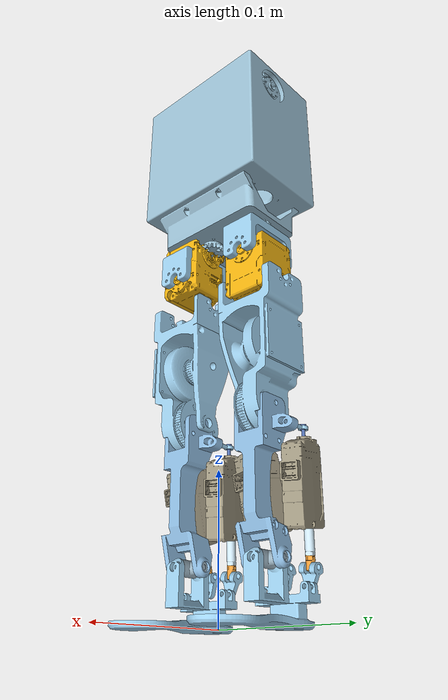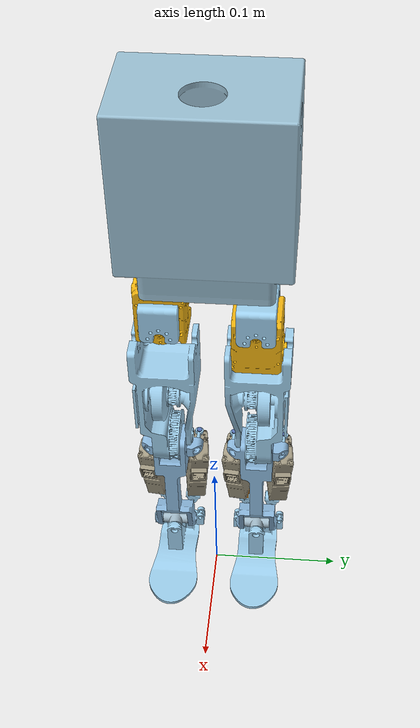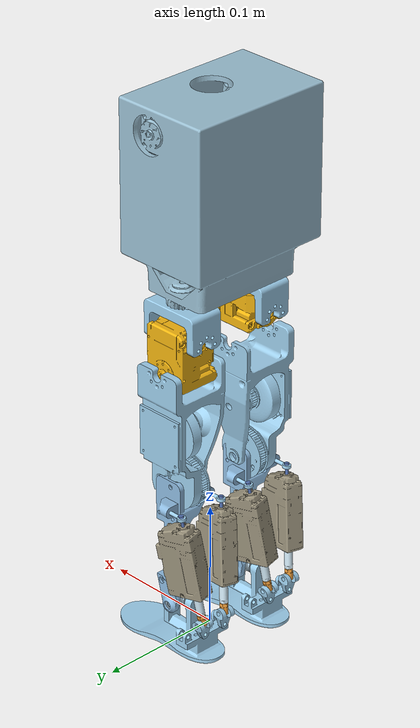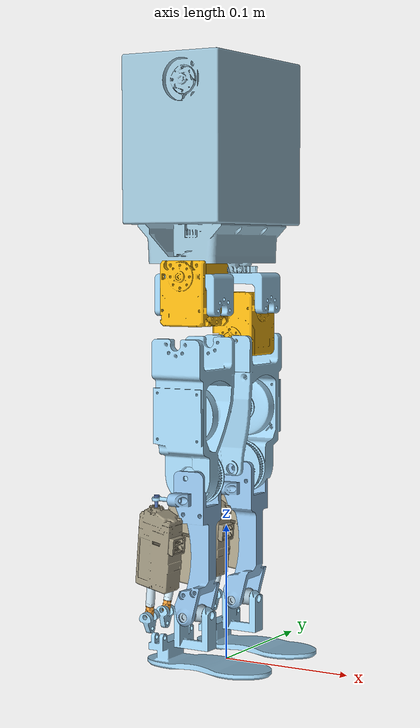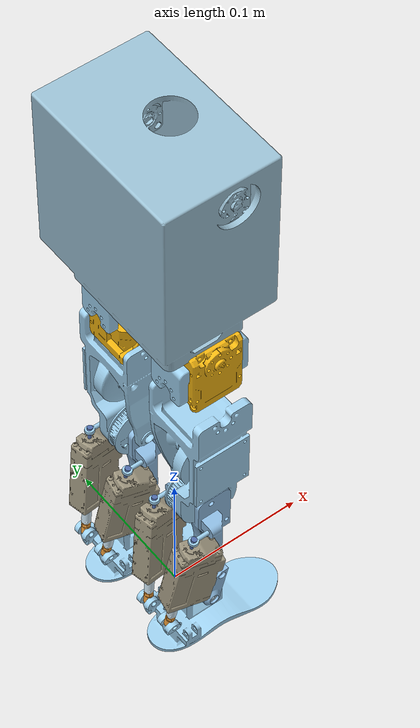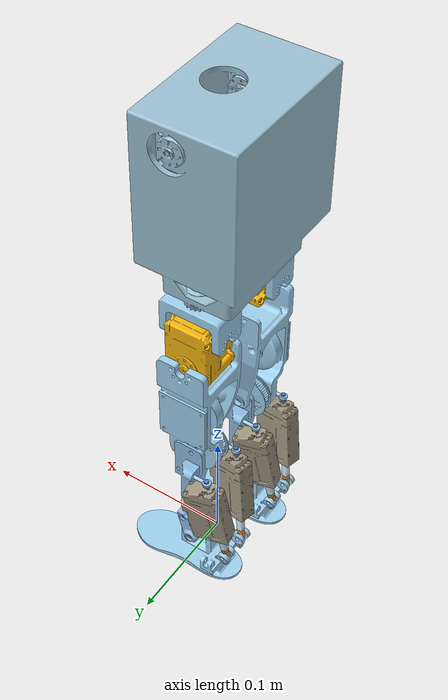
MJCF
<mujoco model="toddlerbot_legs">
  <compiler angle="radian" />
  <asset>
    <mesh name="body_link_visual" file="../assemblies/no_body/meshes/body_link_visual.stl" />
    <mesh name="body_link_collision" file="collisions/body_link_collision.stl" />
    <mesh name="left_hip_yaw_link_visual" file="../assemblies/left_3R+RH5_leg/meshes/left_hip_yaw_link_visual.stl" />
    <mesh name="left_hip_roll_link_visual" file="../assemblies/left_3R+RH5_leg/meshes/left_hip_roll_link_visual.stl" />
    <mesh name="left_hip_roll_link_collision" file="collisions/left_hip_roll_link_collision.stl" />
    <mesh name="left_hip_pitch_link_visual" file="../assemblies/left_3R+RH5_leg/meshes/left_hip_pitch_link_visual.stl" />
    <mesh name="left_hip_pitch_link_collision" file="collisions/left_hip_pitch_link_collision.stl" />
    <mesh name="left_calf_link_visual" file="../assemblies/left_3R+RH5_leg/meshes/left_calf_link_visual.stl" />
    <mesh name="left_calf_link_collision" file="collisions/left_calf_link_collision.stl" />
    <mesh name="left_ank_pitch_link_visual" file="../assemblies/left_3R+RH5_leg/meshes/left_ank_pitch_link_visual.stl" />
    <mesh name="left_ank_roll_link_visual" file="../assemblies/left_3R+RH5_leg/meshes/left_ank_roll_link_visual.stl" />
    <mesh name="left_ank_roll_link_collision" file="collisions/left_ank_roll_link_collision.stl" />
    <mesh name="left_ank_rr_link_visual" file="../assemblies/left_3R+RH5_leg/meshes/left_ank_rr_link_visual.stl" />
    <mesh name="left_12lf_rod_end_visual" file="../assemblies/left_3R+RH5_leg/meshes/left_12lf_rod_end_visual.stl" />
    <mesh name="left_ank_rr_link_2_visual" file="../assemblies/left_3R+RH5_leg/meshes/left_ank_rr_link_2_visual.stl" />
    <mesh name="left_12lf_rod_end_2_visual" file="../assemblies/left_3R+RH5_leg/meshes/left_12lf_rod_end_2_visual.stl" />
    <mesh name="left_ball_joint_container_visual" file="../assemblies/left_3R+RH5_leg/meshes/left_ball_joint_container_visual.stl" />
    <mesh name="left_ball_joint_ball_visual" file="../assemblies/left_3R+RH5_leg/meshes/left_ball_joint_ball_visual.stl" />
    <mesh name="left_12lf_visual" file="../assemblies/left_3R+RH5_leg/meshes/left_12lf_visual.stl" />
    <mesh name="left_12lf_rod_visual" file="../assemblies/left_3R+RH5_leg/meshes/left_12lf_rod_visual.stl" />
    <mesh name="left_ball_joint_container_2_visual" file="../assemblies/left_3R+RH5_leg/meshes/left_ball_joint_container_2_visual.stl" />
    <mesh name="left_ball_joint_ball_2_visual" file="../assemblies/left_3R+RH5_leg/meshes/left_ball_joint_ball_2_visual.stl" />
    <mesh name="left_12lf_2_visual" file="../assemblies/left_3R+RH5_leg/meshes/left_12lf_2_visual.stl" />
    <mesh name="left_12lf_rod_2_visual" file="../assemblies/left_3R+RH5_leg/meshes/left_12lf_rod_2_visual.stl" />
    <mesh name="right_hip_yaw_link_visual" file="../assemblies/right_3R+RH5_leg/meshes/right_hip_yaw_link_visual.stl" />
    <mesh name="right_hip_roll_link_visual" file="../assemblies/right_3R+RH5_leg/meshes/right_hip_roll_link_visual.stl" />
    <mesh name="right_hip_roll_link_collision" file="collisions/right_hip_roll_link_collision.stl" />
    <mesh name="right_hip_pitch_link_visual" file="../assemblies/right_3R+RH5_leg/meshes/right_hip_pitch_link_visual.stl" />
    <mesh name="right_hip_pitch_link_collision" file="collisions/right_hip_pitch_link_collision.stl" />
    <mesh name="right_calf_link_visual" file="../assemblies/right_3R+RH5_leg/meshes/right_calf_link_visual.stl" />
    <mesh name="right_calf_link_collision" file="collisions/right_calf_link_collision.stl" />
    <mesh name="right_ank_pitch_link_visual" file="../assemblies/right_3R+RH5_leg/meshes/right_ank_pitch_link_visual.stl" />
    <mesh name="right_ank_roll_link_visual" file="../assemblies/right_3R+RH5_leg/meshes/right_ank_roll_link_visual.stl" />
    <mesh name="right_ank_roll_link_collision" file="collisions/right_ank_roll_link_collision.stl" />
    <mesh name="right_ank_rr_link_visual" file="../assemblies/right_3R+RH5_leg/meshes/right_ank_rr_link_visual.stl" />
    <mesh name="right_12lf_rod_end_visual" file="../assemblies/right_3R+RH5_leg/meshes/right_12lf_rod_end_visual.stl" />
    <mesh name="right_ank_rr_link_2_visual" file="../assemblies/right_3R+RH5_leg/meshes/right_ank_rr_link_2_visual.stl" />
    <mesh name="right_12lf_rod_end_2_visual" file="../assemblies/right_3R+RH5_leg/meshes/right_12lf_rod_end_2_visual.stl" />
    <mesh name="right_ball_joint_container_visual" file="../assemblies/right_3R+RH5_leg/meshes/right_ball_joint_container_visual.stl" />
    <mesh name="right_ball_joint_ball_visual" file="../assemblies/right_3R+RH5_leg/meshes/right_ball_joint_ball_visual.stl" />
    <mesh name="right_12lf_visual" file="../assemblies/right_3R+RH5_leg/meshes/right_12lf_visual.stl" />
    <mesh name="right_12lf_rod_visual" file="../assemblies/right_3R+RH5_leg/meshes/right_12lf_rod_visual.stl" />
    <mesh name="right_ball_joint_container_2_visual" file="../assemblies/right_3R+RH5_leg/meshes/right_ball_joint_container_2_visual.stl" />
    <mesh name="right_ball_joint_ball_2_visual" file="../assemblies/right_3R+RH5_leg/meshes/right_ball_joint_ball_2_visual.stl" />
    <mesh name="right_12lf_2_visual" file="../assemblies/right_3R+RH5_leg/meshes/right_12lf_2_visual.stl" />
    <mesh name="right_12lf_rod_2_visual" file="../assemblies/right_3R+RH5_leg/meshes/right_12lf_rod_2_visual.stl" />
  </asset>
  <worldbody>
    <site name="torso" fromto="0.01 0 0.4 -0.01 0 0.4" type="cylinder" size="0.005 0.005 1" group="3" />
    <geom rgba="0.602652 0.747582 0.822925 1" mesh="body_link_visual" class="visual" />
    <geom rgba="0.602652 0.747582 0.822925 1" mesh="body_link_collision" class="collision" />
    <body name="hip_yaw_link" pos="-0.0064 0.034 0.2855" quat="1 0 0 0">
      <inertial pos="0 0 -0.00983905" quat="0 0.707107 0 0.707107" mass="0.00902588" diaginertia="3.87214e-06 3.84085e-06 1.32305e-06" />
      <joint name="left_hip_yaw" pos="0 0 0" axis="0 0 1" limited="true" range="-0.785398 0.785398" damping="0.077" armature="0.0034000000000000002" frictionloss="0.0434" />
      <geom rgba="0.615686 0.811765 0.929412 1" mesh="left_hip_yaw_link_visual" class="visual" />
      <body name="hip_roll_link" pos="0.019 0 -0.026" quat="0 0.707107 0 0.707107">
        <inertial pos="-0.0120002 -0.000495888 -0.018504" quat="0.654458 0.267712 0.652088 0.27349" mass="0.0980124" diaginertia="2.78674e-05 2.68492e-05 2.02212e-05" />
        <joint name="left_hip_roll" pos="0 0 0" axis="0 0 1" limited="true" range="-0.785398 1.5708" damping="3.122" armature="0.1" frictionloss="0.0002" />
        <geom rgba="0.950187 0.706789 0.0616121 1" mesh="left_hip_roll_link_visual" class="visual" />
        <geom rgba="0.950187 0.706789 0.0616121 1" mesh="left_hip_roll_link_collision" class="collision" />
        <body name="left_hip_pitch_link" pos="-0.024 -0.019 -0.019" quat="0.5 -0.5 0.5 0.5">
          <inertial pos="-0.000219373 0.0528645 0.0147109" quat="0.670209 0.691924 0.196498 -0.182892" mass="0.0935391" diaginertia="6.26008e-05 6.22249e-05 2.14423e-05" />
          <joint name="left_hip_pitch" pos="0 0 0" axis="0 0 1" limited="true" range="-1.5708 1.5708" damping="1.286" armature="0.0032" frictionloss="0.0" />
          <geom rgba="0.616541 0.807276 0.921717 1" mesh="left_hip_pitch_link_visual" class="visual" />
          <geom rgba="0.616541 0.807276 0.921717 1" mesh="left_hip_pitch_link_collision" class="collision" />
          <body name="left_calf_link" pos="0 0.096 0.0274" quat="0 1 0 0">
            <inertial pos="-0.00391362 -0.04364 0.00818493" quat="0.707645 0.706509 -0.0088213 -0.00239695" mass="0.0162906" diaginertia="1.55474e-05 1.48072e-05 1.93298e-06" />
            <joint name="left_knee" pos="0 0 0" axis="0 0 1" limited="true" range="0 1.5708" damping="1.1420000000000001" armature="0.0" frictionloss="0.031900000000000005" />
            <geom rgba="0.553972 0.731614 0.877157 1" mesh="left_calf_link_visual" class="visual" />
            <geom rgba="0.553972 0.731614 0.877157 1" mesh="left_calf_link_collision" class="collision" />
            <body name="ank_pitch_link" pos="0 -0.1 -0.0062" quat="0 0.707107 -0.707107 0">
              <inertial pos="4.02697e-08 0.000595283 -0.0145999" quat="1 0 -2.35914e-06 0" mass="0.00422384" diaginertia="4.37053e-07 3.97827e-07 8.88586e-08" />
              <joint name="left_ank_pitch" pos="0 0 0" axis="0 0 1" limited="true" range="-0.523599 0.523599" damping="0.523" armature="0.0115" frictionloss="0.0005" />
              <geom rgba="0.631892 0.726687 0.783564 1" mesh="left_ank_pitch_link_visual" class="visual" />
              <body name="ank_roll_link" pos="0 0.0015 -0.0146" quat="0.5 -0.5 -0.5 -0.5">
                <inertial pos="-0.00679543 0.0308001 -0.00196459" quat="0.810294 -0.0798422 -0.00782205 0.580506" mass="0.0212106" diaginertia="1.92447e-05 1.64824e-05 7.29055e-06" />
                <joint name="left_ank_roll" pos="0 0 0" axis="0 0 1" limited="true" range="-0.785398 0.785398" damping="0.583" armature="0.0158" frictionloss="0.00030000000000000003" />
                <geom rgba="0.615686 0.811765 0.929412 1" mesh="left_ank_roll_link_visual" class="visual" />
                <geom rgba="0.615686 0.811765 0.929412 1" mesh="left_ank_roll_link_collision" class="collision" />
                <body name="ank_rr_link" pos="-0.01 0.0125 -0.0336" quat="0.998721 0 0 -0.0505586">
                  <inertial pos="0 -0.00614477 0" quat="0.5 0.5 -0.5 0.5" mass="0.000425071" diaginertia="1.25044e-08 8.78432e-09 8.03017e-09" />
                  <joint name="left_ank_R11" pos="0 0 0" axis="0 0 1" limited="true" range="-1.5708 1.5708" />
                  <geom rgba="0.615686 0.811765 0.929412 1" mesh="left_ank_rr_link_visual" class="visual" />
                  <body name="12lf_rod_end" pos="0 -0.01 0" quat="0.70532 -0.0502423 -0.70532 0.0502423">
                    <inertial pos="-4.47352e-11 -0.00384222 6.43842e-06" quat="0.500199 0.499801 -0.499801 0.500199" mass="0.000854205" diaginertia="1.27035e-08 1.1841e-08 3.35496e-09" />
                    <joint name="left_ank_R21" pos="0 0 0" axis="0 0 1" limited="true" range="-1.5708 1.5708" />
                    <geom rgba="0.927718 0.610493 0.218477 1" mesh="left_12lf_rod_end_visual" class="visual" />
                  </body>
                </body>
                <body name="ank_rr_link_2" pos="0.01 0.0125 -0.0336" quat="0 0.0504983 -0.998724 0">
                  <inertial pos="0 -0.00614477 0" quat="0.5 0.5 -0.5 0.5" mass="0.000425071" diaginertia="1.25044e-08 8.78432e-09 8.03017e-09" />
                  <joint name="left_ank_R12" pos="0 0 0" axis="0 0 1" limited="true" range="-1.5708 1.5708" />
                  <geom rgba="0.615686 0.811765 0.929412 1" mesh="left_ank_rr_link_2_visual" class="visual" />
                  <body name="12lf_rod_end_2" pos="0 -0.01 0" quat="0.705319 0.0502506 -0.705319 -0.0502506">
                    <inertial pos="-4.47352e-11 -0.00384222 6.43842e-06" quat="0.500199 0.499801 -0.499801 0.500199" mass="0.000854205" diaginertia="1.27035e-08 1.1841e-08 3.35496e-09" />
                    <joint name="left_ank_R22" pos="0 0 0" axis="0 0 1" limited="true" range="-1.5708 1.5708" />
                    <geom rgba="0.927718 0.610493 0.218477 1" mesh="left_12lf_rod_end_2_visual" class="visual" />
                  </body>
                </body>
              </body>
            </body>
            <body name="ball_joint_container" pos="0.008 -0.015 0.0283" quat="0.0357503 -0.706202 -0.0357503 0.706202">
              <inertial pos="0 0 -0.00971253" quat="0.707107 0 0 0.707107" mass="4.80374e-05" diaginertia="8.47542e-10 7.18655e-10 1.86253e-10" />
              <joint name="left_ank_B11" pos="0 0 0" axis="0 0 1" limited="true" range="-0.785398 0.785398" />
              <geom rgba="0.615686 0.811765 0.929412 1" mesh="left_ball_joint_container_visual" class="visual" />
              <body name="ball_joint_ball" pos="0 0 -0.0115" quat="0.0502423 0.70532 0.0502423 0.70532">
                <inertial pos="0 -0.00103087 0" quat="0.707107 0.707107 0 0" mass="4.40538e-05" diaginertia="3.1285e-10 3.12853e-10 6.25696e-11" />
                <joint name="left_ank_B21" pos="0 0 0" axis="0 0 1" limited="true" range="-0.785398 0.785398" />
                <geom rgba="0.32913 0.443105 0.692049 1" mesh="left_ball_joint_ball_visual" class="visual" />
                <body name="12lf" pos="0 -0.00643875 0" quat="0.70458 -0.70458 0.0597268 0.0597268">
                  <inertial pos="0.00490842 -0.000138024 -0.029947" quat="0.709913 0.00132323 0.0043477 0.704274" mass="0.0447822" diaginertia="1.81889e-05 1.52606e-05 5.14874e-06" />
                  <joint name="left_ank_B31" pos="0 0 0" axis="0 0 1" limited="true" range="-0.785398 0.785398" />
                  <geom rgba="0.620044 0.588367 0.498971 1" mesh="left_12lf_visual" class="visual" />
                  <body name="12lf_rod" pos="2.27221e-06 0 -0.07266" quat="0 -0.452653 0.891687 0">
                    <inertial pos="-6.32221e-07 4.69333e-07 -0.0128934" quat="1 -2.00488e-05 -2.69482e-05 -5.4028e-10" mass="0.00250883" diaginertia="2.69445e-07 2.69445e-07 1.78098e-08" />
                    <joint name="left_ank_act1" pos="0 0 0" axis="0 0 1" type="slide" limited="true" range="0 0.04" />
                    <geom rgba="0.802503 0.893406 0.944918 1" mesh="left_12lf_rod_visual" class="visual" />
                  </body>
                </body>
              </body>
            </body>
            <body name="ball_joint_container_2" pos="0.008 -0.015 -0.0115" quat="0.706205 -0.0357077 -0.706205 0.0357077">
              <inertial pos="0 0 -0.00971253" quat="0.707107 0 0 0.707107" mass="4.80374e-05" diaginertia="8.47542e-10 7.18655e-10 1.86253e-10" />
              <joint name="left_ank_B12" pos="0 0 0" axis="0 0 1" limited="true" range="-0.785398 0.785398" />
              <geom rgba="0.615686 0.811765 0.929412 1" mesh="left_ball_joint_container_2_visual" class="visual" />
              <body name="ball_joint_ball_2" pos="0 0 -0.0115" quat="0.705319 0.0502506 -0.705319 -0.0502506">
                <inertial pos="0 -0.00103087 0" quat="0.707107 0.707107 0 0" mass="4.40538e-05" diaginertia="3.1285e-10 3.12853e-10 6.25696e-11" />
                <joint name="left_ank_B22" pos="0 0 0" axis="0 0 1" limited="true" range="-0.785398 0.785398" />
                <geom rgba="0.32913 0.443105 0.692049 1" mesh="left_ball_joint_ball_2_visual" class="visual" />
                <body name="12lf_2" pos="0 -0.00643875 0" quat="0.704247 -0.704247 -0.0635296 -0.0635296">
                  <inertial pos="0.00490842 -0.000138024 -0.029947" quat="0.709913 0.00132323 0.0043477 0.704274" mass="0.0447822" diaginertia="1.81889e-05 1.52606e-05 5.14874e-06" />
                  <joint name="left_ank_B32" pos="0 0 0" axis="0 0 1" limited="true" range="-0.785398 0.785398" />
                  <geom rgba="0.620044 0.588367 0.498971 1" mesh="left_12lf_2_visual" class="visual" />
                  <body name="12lf_rod_2" pos="2.27221e-06 0 -0.07266" quat="0 -0.452653 0.891687 0">
                    <inertial pos="-6.32221e-07 4.69333e-07 -0.0128934" quat="1 -2.00488e-05 -2.69482e-05 -5.4028e-10" mass="0.00250883" diaginertia="2.69445e-07 2.69445e-07 1.78098e-08" />
                    <joint name="left_ank_act2" pos="0 0 0" axis="0 0 1" type="slide" limited="true" range="0 0.04" />
                    <geom rgba="0.802503 0.893406 0.944918 1" mesh="left_12lf_rod_2_visual" class="visual" />
                  </body>
                </body>
              </body>
            </body>
          </body>
        </body>
      </body>
    </body>
    <body name="hip_yaw_link_2" pos="-0.0064 -0.034 0.2855" quat="1 0 0 0">
      <inertial pos="0 0 -0.00983905" quat="0 0.707107 0 0.707107" mass="0.00902588" diaginertia="3.87214e-06 3.84085e-06 1.32305e-06" />
      <joint name="right_hip_yaw" pos="0 0 0" axis="0 0 1" limited="true" range="-0.785398 0.785398" damping="0.077" armature="0.0034000000000000002" frictionloss="0.0434" />
      <geom rgba="0.615686 0.811765 0.929412 1" mesh="right_hip_yaw_link_visual" class="visual" />
      <body name="hip_roll_link_2" pos="0.019 0 -0.026" quat="0.707107 0 0.707107 0">
        <inertial pos="0.0120002 -0.000495888 -0.019496" quat="0.27349 0.652088 0.267712 0.654458" mass="0.0980124" diaginertia="2.78674e-05 2.68492e-05 2.02212e-05" />
        <joint name="right_hip_roll" pos="0 0 0" axis="0 0 1" limited="true" range="-1.5708 0.785398" damping="3.122" armature="0.1" frictionloss="0.0002" />
        <geom rgba="0.950187 0.706789 0.0616121 1" mesh="right_hip_roll_link_visual" class="visual" />
        <geom rgba="0.950187 0.706789 0.0616121 1" mesh="right_hip_roll_link_collision" class="collision" />
        <body name="right_hip_pitch_link" pos="0.024 -0.019 -0.019" quat="0.5 -0.5 -0.5 -0.5">
          <inertial pos="-1.30438e-05 0.0528645 0.0147109" quat="0.694626 0.71927 0.0065765 -0.0101395" mass="0.0935391" diaginertia="6.24972e-05 6.23298e-05 2.145e-05" />
          <joint name="right_hip_pitch" pos="0 0 0" axis="0 0 1" limited="true" range="-1.5708 1.5708" damping="1.286" armature="0.0032" frictionloss="0.0" />
          <geom rgba="0.616541 0.807276 0.921717 1" mesh="right_hip_pitch_link_visual" class="visual" />
          <geom rgba="0.616541 0.807276 0.921717 1" mesh="right_hip_pitch_link_collision" class="collision" />
          <body name="right_calf_link" pos="0 0.096 0.0274" quat="0 0 1 0">
            <inertial pos="-0.0039136 0.04364 0.0081849" quat="0.706509 0.707645 0.00239487 0.00882362" mass="0.0162906" diaginertia="1.55475e-05 1.48072e-05 1.933e-06" />
            <joint name="right_knee" pos="0 0 0" axis="0 0 1" limited="true" range="-1.5708 0" damping="1.1420000000000001" armature="0.0" frictionloss="0.031900000000000005" />
            <geom rgba="0.553972 0.731614 0.877157 1" mesh="right_calf_link_visual" class="visual" />
            <geom rgba="0.553972 0.731614 0.877157 1" mesh="right_calf_link_collision" class="collision" />
            <body name="ank_pitch_link_2" pos="0 0.1 -0.0062" quat="0 -0.707107 0.707107 0">
              <inertial pos="4.02697e-08 0.000595283 -0.0145999" quat="1 0 -2.35914e-06 0" mass="0.00422384" diaginertia="4.37053e-07 3.97827e-07 8.88586e-08" />
              <joint name="right_ank_pitch" pos="0 0 0" axis="0 0 1" limited="true" range="-0.523599 0.523599" damping="0.523" armature="0.0115" frictionloss="0.0005" />
              <geom rgba="0.631892 0.726687 0.783564 1" mesh="right_ank_pitch_link_visual" class="visual" />
              <body name="ank_roll_link_2" pos="0 0.0015 -0.0146" quat="0.5 -0.5 0.5 0.5">
                <inertial pos="0.00679543 0.0308001 -0.00196459" quat="0.580506 0.00782207 0.0798423 0.810294" mass="0.0212106" diaginertia="1.92447e-05 1.64824e-05 7.29055e-06" />
                <joint name="right_ank_roll" pos="0 0 0" axis="0 0 1" limited="true" range="-0.785398 0.785398" damping="0.583" armature="0.0158" frictionloss="0.00030000000000000003" />
                <geom rgba="0.615686 0.811765 0.929412 1" mesh="right_ank_roll_link_visual" class="visual" />
                <geom rgba="0.615686 0.811765 0.929412 1" mesh="right_ank_roll_link_collision" class="collision" />
                <body name="ank_rr_link_3" pos="-0.01 0.0125 -0.0336" quat="0.998721 0 0 -0.0505586">
                  <inertial pos="0 -0.00614477 0" quat="0.5 0.5 -0.5 0.5" mass="0.000425071" diaginertia="1.25044e-08 8.78432e-09 8.03017e-09" />
                  <joint name="right_ank_R11" pos="0 0 0" axis="0 0 1" limited="true" range="-1.5708 1.5708" />
                  <geom rgba="0.615686 0.811765 0.929412 1" mesh="right_ank_rr_link_visual" class="visual" />
                  <body name="12lf_rod_end_3" pos="0 -0.01 0" quat="0.70532 -0.0502423 -0.70532 0.0502423">
                    <inertial pos="-4.47352e-11 -0.00384222 6.43842e-06" quat="0.500199 0.499801 -0.499801 0.500199" mass="0.000854205" diaginertia="1.27035e-08 1.1841e-08 3.35496e-09" />
                    <joint name="right_ank_R21" pos="0 0 0" axis="0 0 1" limited="true" range="-1.5708 1.5708" />
                    <geom rgba="0.927718 0.610493 0.218477 1" mesh="right_12lf_rod_end_visual" class="visual" />
                  </body>
                </body>
                <body name="ank_rr_link_4" pos="0.01 0.0125 -0.0336" quat="0 -0.0504983 0.998724 0">
                  <inertial pos="0 -0.00614477 0" quat="0.5 0.5 -0.5 0.5" mass="0.000425071" diaginertia="1.25044e-08 8.78432e-09 8.03017e-09" />
                  <joint name="right_ank_R12" pos="0 0 0" axis="0 0 1" limited="true" range="-1.5708 1.5708" />
                  <geom rgba="0.615686 0.811765 0.929412 1" mesh="right_ank_rr_link_2_visual" class="visual" />
                  <body name="12lf_rod_end_4" pos="0 -0.01 0" quat="0.705319 0.0502506 -0.705319 -0.0502506">
                    <inertial pos="-4.47352e-11 -0.00384222 6.43842e-06" quat="0.500199 0.499801 -0.499801 0.500199" mass="0.000854205" diaginertia="1.27035e-08 1.1841e-08 3.35496e-09" />
                    <joint name="right_ank_R22" pos="0 0 0" axis="0 0 1" limited="true" range="-1.5708 1.5708" />
                    <geom rgba="0.927718 0.610493 0.218477 1" mesh="right_12lf_rod_end_2_visual" class="visual" />
                  </body>
                </body>
              </body>
            </body>
            <body name="ball_joint_container_3" pos="0.008 0.015 -0.0115" quat="0.706202 0.0357503 -0.706202 -0.0357503">
              <inertial pos="0 0 -0.00971253" quat="0.707107 0 0 0.707107" mass="4.80374e-05" diaginertia="8.47542e-10 7.18655e-10 1.86253e-10" />
              <joint name="right_ank_B11" pos="0 0 0" axis="0 0 1" limited="true" range="-0.785398 0.785398" />
              <geom rgba="0.615686 0.811765 0.929412 1" mesh="right_ball_joint_container_visual" class="visual" />
              <body name="ball_joint_ball_3" pos="0 0 -0.0115" quat="0.0502423 0.70532 0.0502423 0.70532">
                <inertial pos="0 -0.00103087 0" quat="0.707107 0.707107 0 0" mass="4.40538e-05" diaginertia="3.1285e-10 3.12853e-10 6.25696e-11" />
                <joint name="right_ank_B21" pos="0 0 0" axis="0 0 1" limited="true" range="-0.785398 0.785398" />
                <geom rgba="0.32913 0.443105 0.692049 1" mesh="right_ball_joint_ball_visual" class="visual" />
                <body name="12lf_3" pos="0 -0.00643875 0" quat="0.70458 -0.70458 0.0597268 0.0597268">
                  <inertial pos="0.00490842 -0.000138024 -0.029947" quat="0.709913 0.00132323 0.0043477 0.704274" mass="0.0447822" diaginertia="1.81889e-05 1.52606e-05 5.14874e-06" />
                  <joint name="right_ank_B31" pos="0 0 0" axis="0 0 1" limited="true" range="-0.785398 0.785398" />
                  <geom rgba="0.620044 0.588367 0.498971 1" mesh="right_12lf_visual" class="visual" />
                  <body name="12lf_rod_3" pos="2.27221e-06 0 -0.07266" quat="0 -0.452653 0.891687 0">
                    <inertial pos="-6.32221e-07 4.69333e-07 -0.0128934" quat="1 -2.00488e-05 -2.69482e-05 -5.4028e-10" mass="0.00250883" diaginertia="2.69445e-07 2.69445e-07 1.78098e-08" />
                    <joint name="right_ank_act1" pos="0 0 0" axis="0 0 1" type="slide" limited="true" range="0 0.04" />
                    <geom rgba="0.802503 0.893406 0.944918 1" mesh="right_12lf_rod_visual" class="visual" />
                  </body>
                </body>
              </body>
            </body>
            <body name="ball_joint_container_4" pos="0.008 0.015 0.0283" quat="0.706205 -0.0357077 -0.706205 0.0357077">
              <inertial pos="0 0 -0.00971253" quat="0.707107 0 0 0.707107" mass="4.80374e-05" diaginertia="8.47542e-10 7.18655e-10 1.86253e-10" />
              <joint name="right_ank_B12" pos="0 0 0" axis="0 0 1" limited="true" range="-0.785398 0.785398" />
              <geom rgba="0.615686 0.811765 0.929412 1" mesh="right_ball_joint_container_2_visual" class="visual" />
              <body name="ball_joint_ball_4" pos="0 0 -0.0115" quat="0.0502506 0.705319 0.0502506 0.705319">
                <inertial pos="0 -0.00103087 0" quat="0.707107 0.707107 0 0" mass="4.40538e-05" diaginertia="3.1285e-10 3.12853e-10 6.25696e-11" />
                <joint name="right_ank_B22" pos="0 0 0" axis="0 0 1" limited="true" range="-0.785398 0.785398" />
                <geom rgba="0.32913 0.443105 0.692049 1" mesh="right_ball_joint_ball_2_visual" class="visual" />
                <body name="12lf_4" pos="0 -0.00643875 0" quat="0.704247 -0.704247 -0.0635296 -0.0635296">
                  <inertial pos="0.00490842 -0.000138024 -0.029947" quat="0.709913 0.00132323 0.0043477 0.704274" mass="0.0447822" diaginertia="1.81889e-05 1.52606e-05 5.14874e-06" />
                  <joint name="right_ank_B32" pos="0 0 0" axis="0 0 1" limited="true" range="-0.785398 0.785398" />
                  <geom rgba="0.620044 0.588367 0.498971 1" mesh="right_12lf_2_visual" class="visual" />
                  <body name="12lf_rod_4" pos="2.27221e-06 0 -0.07266" quat="0 0.452653 -0.891687 0">
                    <inertial pos="-6.32221e-07 4.69333e-07 -0.0128934" quat="1 -2.00488e-05 -2.69482e-05 -5.4028e-10" mass="0.00250883" diaginertia="2.69445e-07 2.69445e-07 1.78098e-08" />
                    <joint name="right_ank_act2" pos="0 0 0" axis="0 0 1" type="slide" limited="true" range="0 0.04" />
                    <geom rgba="0.802503 0.893406 0.944918 1" mesh="right_12lf_rod_2_visual" class="visual" />
                  </body>
                </body>
              </body>
            </body>
          </body>
        </body>
      </body>
    </body>
  </worldbody>
  <contact>
    <exclude body1="hip_yaw_link" body2="hip_roll_link" />
    <exclude body1="hip_yaw_link" body2="left_hip_pitch_link" />
    <exclude body1="hip_yaw_link" body2="left_calf_link" />
    <exclude body1="hip_yaw_link" body2="ank_pitch_link" />
    <exclude body1="hip_yaw_link" body2="ank_roll_link" />
    <exclude body1="hip_yaw_link" body2="ank_rr_link" />
    <exclude body1="hip_yaw_link" body2="12lf_rod_end" />
    <exclude body1="hip_yaw_link" body2="ank_rr_link_2" />
    <exclude body1="hip_yaw_link" body2="12lf_rod_end_2" />
    <exclude body1="hip_yaw_link" body2="ball_joint_container" />
    <exclude body1="hip_yaw_link" body2="ball_joint_ball" />
    <exclude body1="hip_yaw_link" body2="12lf" />
    <exclude body1="hip_yaw_link" body2="12lf_rod" />
    <exclude body1="hip_yaw_link" body2="ball_joint_container_2" />
    <exclude body1="hip_yaw_link" body2="ball_joint_ball_2" />
    <exclude body1="hip_yaw_link" body2="12lf_2" />
    <exclude body1="hip_yaw_link" body2="12lf_rod_2" />
    <exclude body1="hip_yaw_link" body2="hip_yaw_link_2" />
    <exclude body1="hip_yaw_link" body2="hip_roll_link_2" />
    <exclude body1="hip_yaw_link" body2="right_hip_pitch_link" />
    <exclude body1="hip_yaw_link" body2="right_calf_link" />
    <exclude body1="hip_yaw_link" body2="ank_pitch_link_2" />
    <exclude body1="hip_yaw_link" body2="ank_roll_link_2" />
    <exclude body1="hip_yaw_link" body2="ank_rr_link_3" />
    <exclude body1="hip_yaw_link" body2="12lf_rod_end_3" />
    <exclude body1="hip_yaw_link" body2="ank_rr_link_4" />
    <exclude body1="hip_yaw_link" body2="12lf_rod_end_4" />
    <exclude body1="hip_yaw_link" body2="ball_joint_container_3" />
    <exclude body1="hip_yaw_link" body2="ball_joint_ball_3" />
    <exclude body1="hip_yaw_link" body2="12lf_3" />
    <exclude body1="hip_yaw_link" body2="12lf_rod_3" />
    <exclude body1="hip_yaw_link" body2="ball_joint_container_4" />
    <exclude body1="hip_yaw_link" body2="ball_joint_ball_4" />
    <exclude body1="hip_yaw_link" body2="12lf_4" />
    <exclude body1="hip_yaw_link" body2="12lf_rod_4" />
    <exclude body1="hip_roll_link" body2="hip_yaw_link" />
    <exclude body1="hip_roll_link" body2="left_hip_pitch_link" />
    <exclude body1="hip_roll_link" body2="left_calf_link" />
    <exclude body1="hip_roll_link" body2="ank_pitch_link" />
    <exclude body1="hip_roll_link" body2="ank_roll_link" />
    <exclude body1="hip_roll_link" body2="ank_rr_link" />
    <exclude body1="hip_roll_link" body2="12lf_rod_end" />
    <exclude body1="hip_roll_link" body2="ank_rr_link_2" />
    <exclude body1="hip_roll_link" body2="12lf_rod_end_2" />
    <exclude body1="hip_roll_link" body2="ball_joint_container" />
    <exclude body1="hip_roll_link" body2="ball_joint_ball" />
    <exclude body1="hip_roll_link" body2="12lf" />
    <exclude body1="hip_roll_link" body2="12lf_rod" />
    <exclude body1="hip_roll_link" body2="ball_joint_container_2" />
    <exclude body1="hip_roll_link" body2="ball_joint_ball_2" />
    <exclude body1="hip_roll_link" body2="12lf_2" />
    <exclude body1="hip_roll_link" body2="12lf_rod_2" />
    <exclude body1="hip_roll_link" body2="hip_yaw_link_2" />
    <exclude body1="hip_roll_link" body2="hip_roll_link_2" />
    <exclude body1="hip_roll_link" body2="right_hip_pitch_link" />
    <exclude body1="hip_roll_link" body2="right_calf_link" />
    <exclude body1="hip_roll_link" body2="ank_pitch_link_2" />
    <exclude body1="hip_roll_link" body2="ank_roll_link_2" />
    <exclude body1="hip_roll_link" body2="ank_rr_link_3" />
    <exclude body1="hip_roll_link" body2="12lf_rod_end_3" />
    <exclude body1="hip_roll_link" body2="ank_rr_link_4" />
    <exclude body1="hip_roll_link" body2="12lf_rod_end_4" />
    <exclude body1="hip_roll_link" body2="ball_joint_container_3" />
    <exclude body1="hip_roll_link" body2="ball_joint_ball_3" />
    <exclude body1="hip_roll_link" body2="12lf_3" />
    <exclude body1="hip_roll_link" body2="12lf_rod_3" />
    <exclude body1="hip_roll_link" body2="ball_joint_container_4" />
    <exclude body1="hip_roll_link" body2="ball_joint_ball_4" />
    <exclude body1="hip_roll_link" body2="12lf_4" />
    <exclude body1="hip_roll_link" body2="12lf_rod_4" />
    <exclude body1="left_hip_pitch_link" body2="hip_yaw_link" />
    <exclude body1="left_hip_pitch_link" body2="hip_roll_link" />
    <exclude body1="left_hip_pitch_link" body2="left_calf_link" />
    <exclude body1="left_hip_pitch_link" body2="ank_pitch_link" />
    <exclude body1="left_hip_pitch_link" body2="ank_roll_link" />
    <exclude body1="left_hip_pitch_link" body2="ank_rr_link" />
    <exclude body1="left_hip_pitch_link" body2="12lf_rod_end" />
    <exclude body1="left_hip_pitch_link" body2="ank_rr_link_2" />
    <exclude body1="left_hip_pitch_link" body2="12lf_rod_end_2" />
    <exclude body1="left_hip_pitch_link" body2="ball_joint_container" />
    <exclude body1="left_hip_pitch_link" body2="ball_joint_ball" />
    <exclude body1="left_hip_pitch_link" body2="12lf" />
    <exclude body1="left_hip_pitch_link" body2="12lf_rod" />
    <exclude body1="left_hip_pitch_link" body2="ball_joint_container_2" />
    <exclude body1="left_hip_pitch_link" body2="ball_joint_ball_2" />
    <exclude body1="left_hip_pitch_link" body2="12lf_2" />
    <exclude body1="left_hip_pitch_link" body2="12lf_rod_2" />
    <exclude body1="left_hip_pitch_link" body2="hip_yaw_link_2" />
    <exclude body1="left_hip_pitch_link" body2="hip_roll_link_2" />
    <exclude body1="left_hip_pitch_link" body2="right_hip_pitch_link" />
    <exclude body1="left_hip_pitch_link" body2="right_calf_link" />
    <exclude body1="left_hip_pitch_link" body2="ank_pitch_link_2" />
    <exclude body1="left_hip_pitch_link" body2="ank_roll_link_2" />
    <exclude body1="left_hip_pitch_link" body2="ank_rr_link_3" />
    <exclude body1="left_hip_pitch_link" body2="12lf_rod_end_3" />
    <exclude body1="left_hip_pitch_link" body2="ank_rr_link_4" />
    <exclude body1="left_hip_pitch_link" body2="12lf_rod_end_4" />
    <exclude body1="left_hip_pitch_link" body2="ball_joint_container_3" />
    <exclude body1="left_hip_pitch_link" body2="ball_joint_ball_3" />
    <exclude body1="left_hip_pitch_link" body2="12lf_3" />
    <exclude body1="left_hip_pitch_link" body2="12lf_rod_3" />
    <exclude body1="left_hip_pitch_link" body2="ball_joint_container_4" />
    <exclude body1="left_hip_pitch_link" body2="ball_joint_ball_4" />
    <exclude body1="left_hip_pitch_link" body2="12lf_4" />
    <exclude body1="left_hip_pitch_link" body2="12lf_rod_4" />
    <exclude body1="left_calf_link" body2="hip_yaw_link" />
    <exclude body1="left_calf_link" body2="hip_roll_link" />
    <exclude body1="left_calf_link" body2="left_hip_pitch_link" />
    <exclude body1="left_calf_link" body2="ank_pitch_link" />
    <exclude body1="left_calf_link" body2="ank_roll_link" />
    <exclude body1="left_calf_link" body2="ank_rr_link" />
    <exclude body1="left_calf_link" body2="12lf_rod_end" />
    <exclude body1="left_calf_link" body2="ank_rr_link_2" />
    <exclude body1="left_calf_link" body2="12lf_rod_end_2" />
    <exclude body1="left_calf_link" body2="ball_joint_container" />
    <exclude body1="left_calf_link" body2="ball_joint_ball" />
    <exclude body1="left_calf_link" body2="12lf" />
    <exclude body1="left_calf_link" body2="12lf_rod" />
    <exclude body1="left_calf_link" body2="ball_joint_container_2" />
    <exclude body1="left_calf_link" body2="ball_joint_ball_2" />
    <exclude body1="left_calf_link" body2="12lf_2" />
    <exclude body1="left_calf_link" body2="12lf_rod_2" />
    <exclude body1="left_calf_link" body2="hip_yaw_link_2" />
    <exclude body1="left_calf_link" body2="hip_roll_link_2" />
    <exclude body1="left_calf_link" body2="right_hip_pitch_link" />
    <exclude body1="left_calf_link" body2="right_calf_link" />
    <exclude body1="left_calf_link" body2="ank_pitch_link_2" />
    <exclude body1="left_calf_link" body2="ank_roll_link_2" />
    <exclude body1="left_calf_link" body2="ank_rr_link_3" />
    <exclude body1="left_calf_link" body2="12lf_rod_end_3" />
    <exclude body1="left_calf_link" body2="ank_rr_link_4" />
    <exclude body1="left_calf_link" body2="12lf_rod_end_4" />
    <exclude body1="left_calf_link" body2="ball_joint_container_3" />
    <exclude body1="left_calf_link" body2="ball_joint_ball_3" />
    <exclude body1="left_calf_link" body2="12lf_3" />
    <exclude body1="left_calf_link" body2="12lf_rod_3" />
    <exclude body1="left_calf_link" body2="ball_joint_container_4" />
    <exclude body1="left_calf_link" body2="ball_joint_ball_4" />
    <exclude body1="left_calf_link" body2="12lf_4" />
    <exclude body1="left_calf_link" body2="12lf_rod_4" />
    <exclude body1="ank_pitch_link" body2="hip_yaw_link" />
    <exclude body1="ank_pitch_link" body2="hip_roll_link" />
    <exclude body1="ank_pitch_link" body2="left_hip_pitch_link" />
    <exclude body1="ank_pitch_link" body2="left_calf_link" />
    <exclude body1="ank_pitch_link" body2="ank_roll_link" />
    <exclude body1="ank_pitch_link" body2="ank_rr_link" />
    <exclude body1="ank_pitch_link" body2="12lf_rod_end" />
    <exclude body1="ank_pitch_link" body2="ank_rr_link_2" />
    <exclude body1="ank_pitch_link" body2="12lf_rod_end_2" />
    <exclude body1="ank_pitch_link" body2="ball_joint_container" />
    <exclude body1="ank_pitch_link" body2="ball_joint_ball" />
    <exclude body1="ank_pitch_link" body2="12lf" />
    <exclude body1="ank_pitch_link" body2="12lf_rod" />
    <exclude body1="ank_pitch_link" body2="ball_joint_container_2" />
    <exclude body1="ank_pitch_link" body2="ball_joint_ball_2" />
    <exclude body1="ank_pitch_link" body2="12lf_2" />
    <exclude body1="ank_pitch_link" body2="12lf_rod_2" />
    <exclude body1="ank_pitch_link" body2="hip_yaw_link_2" />
    <exclude body1="ank_pitch_link" body2="hip_roll_link_2" />
    <exclude body1="ank_pitch_link" body2="right_hip_pitch_link" />
    <exclude body1="ank_pitch_link" body2="right_calf_link" />
    <exclude body1="ank_pitch_link" body2="ank_pitch_link_2" />
    <exclude body1="ank_pitch_link" body2="ank_roll_link_2" />
    <exclude body1="ank_pitch_link" body2="ank_rr_link_3" />
    <exclude body1="ank_pitch_link" body2="12lf_rod_end_3" />
    <exclude body1="ank_pitch_link" body2="ank_rr_link_4" />
    <exclude body1="ank_pitch_link" body2="12lf_rod_end_4" />
    <exclude body1="ank_pitch_link" body2="ball_joint_container_3" />
    <exclude body1="ank_pitch_link" body2="ball_joint_ball_3" />
    <exclude body1="ank_pitch_link" body2="12lf_3" />
    <exclude body1="ank_pitch_link" body2="12lf_rod_3" />
    <exclude body1="ank_pitch_link" body2="ball_joint_container_4" />
    <exclude body1="ank_pitch_link" body2="ball_joint_ball_4" />
    <exclude body1="ank_pitch_link" body2="12lf_4" />
    <exclude body1="ank_pitch_link" body2="12lf_rod_4" />
    <exclude body1="ank_roll_link" body2="hip_yaw_link" />
    <exclude body1="ank_roll_link" body2="hip_roll_link" />
    <exclude body1="ank_roll_link" body2="left_hip_pitch_link" />
    <exclude body1="ank_roll_link" body2="left_calf_link" />
    <exclude body1="ank_roll_link" body2="ank_pitch_link" />
    <exclude body1="ank_roll_link" body2="ank_rr_link" />
    <exclude body1="ank_roll_link" body2="12lf_rod_end" />
    <exclude body1="ank_roll_link" body2="ank_rr_link_2" />
    <exclude body1="ank_roll_link" body2="12lf_rod_end_2" />
    <exclude body1="ank_roll_link" body2="ball_joint_container" />
    <exclude body1="ank_roll_link" body2="ball_joint_ball" />
    <exclude body1="ank_roll_link" body2="12lf" />
    <exclude body1="ank_roll_link" body2="12lf_rod" />
    <exclude body1="ank_roll_link" body2="ball_joint_container_2" />
    <exclude body1="ank_roll_link" body2="ball_joint_ball_2" />
    <exclude body1="ank_roll_link" body2="12lf_2" />
    <exclude body1="ank_roll_link" body2="12lf_rod_2" />
    <exclude body1="ank_roll_link" body2="hip_yaw_link_2" />
    <exclude body1="ank_roll_link" body2="hip_roll_link_2" />
    <exclude body1="ank_roll_link" body2="right_hip_pitch_link" />
    <exclude body1="ank_roll_link" body2="right_calf_link" />
    <exclude body1="ank_roll_link" body2="ank_pitch_link_2" />
    <exclude body1="ank_roll_link" body2="ank_roll_link_2" />
    <exclude body1="ank_roll_link" body2="ank_rr_link_3" />
    <exclude body1="ank_roll_link" body2="12lf_rod_end_3" />
    <exclude body1="ank_roll_link" body2="ank_rr_link_4" />
    <exclude body1="ank_roll_link" body2="12lf_rod_end_4" />
    <exclude body1="ank_roll_link" body2="ball_joint_container_3" />
    <exclude body1="ank_roll_link" body2="ball_joint_ball_3" />
    <exclude body1="ank_roll_link" body2="12lf_3" />
    <exclude body1="ank_roll_link" body2="12lf_rod_3" />
    <exclude body1="ank_roll_link" body2="ball_joint_container_4" />
    <exclude body1="ank_roll_link" body2="ball_joint_ball_4" />
    <exclude body1="ank_roll_link" body2="12lf_4" />
    <exclude body1="ank_roll_link" body2="12lf_rod_4" />
    <exclude body1="ank_rr_link" body2="hip_yaw_link" />
    <exclude body1="ank_rr_link" body2="hip_roll_link" />
    <exclude body1="ank_rr_link" body2="left_hip_pitch_link" />
    <exclude body1="ank_rr_link" body2="left_calf_link" />
    <exclude body1="ank_rr_link" body2="ank_pitch_link" />
    <exclude body1="ank_rr_link" body2="ank_roll_link" />
    <exclude body1="ank_rr_link" body2="12lf_rod_end" />
    <exclude body1="ank_rr_link" body2="ank_rr_link_2" />
    <exclude body1="ank_rr_link" body2="12lf_rod_end_2" />
    <exclude body1="ank_rr_link" body2="ball_joint_container" />
    <exclude body1="ank_rr_link" body2="ball_joint_ball" />
    <exclude body1="ank_rr_link" body2="12lf" />
    <exclude body1="ank_rr_link" body2="12lf_rod" />
    <exclude body1="ank_rr_link" body2="ball_joint_container_2" />
    <exclude body1="ank_rr_link" body2="ball_joint_ball_2" />
    <exclude body1="ank_rr_link" body2="12lf_2" />
    <exclude body1="ank_rr_link" body2="12lf_rod_2" />
    <exclude body1="ank_rr_link" body2="hip_yaw_link_2" />
    <exclude body1="ank_rr_link" body2="hip_roll_link_2" />
    <exclude body1="ank_rr_link" body2="right_hip_pitch_link" />
    <exclude body1="ank_rr_link" body2="right_calf_link" />
    <exclude body1="ank_rr_link" body2="ank_pitch_link_2" />
    <exclude body1="ank_rr_link" body2="ank_roll_link_2" />
    <exclude body1="ank_rr_link" body2="ank_rr_link_3" />
    <exclude body1="ank_rr_link" body2="12lf_rod_end_3" />
    <exclude body1="ank_rr_link" body2="ank_rr_link_4" />
    <exclude body1="ank_rr_link" body2="12lf_rod_end_4" />
    <exclude body1="ank_rr_link" body2="ball_joint_container_3" />
    <exclude body1="ank_rr_link" body2="ball_joint_ball_3" />
    <exclude body1="ank_rr_link" body2="12lf_3" />
    <exclude body1="ank_rr_link" body2="12lf_rod_3" />
    <exclude body1="ank_rr_link" body2="ball_joint_container_4" />
    <exclude body1="ank_rr_link" body2="ball_joint_ball_4" />
    <exclude body1="ank_rr_link" body2="12lf_4" />
    <exclude body1="ank_rr_link" body2="12lf_rod_4" />
    <exclude body1="12lf_rod_end" body2="hip_yaw_link" />
    <exclude body1="12lf_rod_end" body2="hip_roll_link" />
    <exclude body1="12lf_rod_end" body2="left_hip_pitch_link" />
    <exclude body1="12lf_rod_end" body2="left_calf_link" />
    <exclude body1="12lf_rod_end" body2="ank_pitch_link" />
    <exclude body1="12lf_rod_end" body2="ank_roll_link" />
    <exclude body1="12lf_rod_end" body2="ank_rr_link" />
    <exclude body1="12lf_rod_end" body2="ank_rr_link_2" />
    <exclude body1="12lf_rod_end" body2="12lf_rod_end_2" />
    <exclude body1="12lf_rod_end" body2="ball_joint_container" />
    <exclude body1="12lf_rod_end" body2="ball_joint_ball" />
    <exclude body1="12lf_rod_end" body2="12lf" />
    <exclude body1="12lf_rod_end" body2="12lf_rod" />
    <exclude body1="12lf_rod_end" body2="ball_joint_container_2" />
    <exclude body1="12lf_rod_end" body2="ball_joint_ball_2" />
    <exclude body1="12lf_rod_end" body2="12lf_2" />
    <exclude body1="12lf_rod_end" body2="12lf_rod_2" />
    <exclude body1="12lf_rod_end" body2="hip_yaw_link_2" />
    <exclude body1="12lf_rod_end" body2="hip_roll_link_2" />
    <exclude body1="12lf_rod_end" body2="right_hip_pitch_link" />
    <exclude body1="12lf_rod_end" body2="right_calf_link" />
    <exclude body1="12lf_rod_end" body2="ank_pitch_link_2" />
    <exclude body1="12lf_rod_end" body2="ank_roll_link_2" />
    <exclude body1="12lf_rod_end" body2="ank_rr_link_3" />
    <exclude body1="12lf_rod_end" body2="12lf_rod_end_3" />
    <exclude body1="12lf_rod_end" body2="ank_rr_link_4" />
    <exclude body1="12lf_rod_end" body2="12lf_rod_end_4" />
    <exclude body1="12lf_rod_end" body2="ball_joint_container_3" />
    <exclude body1="12lf_rod_end" body2="ball_joint_ball_3" />
    <exclude body1="12lf_rod_end" body2="12lf_3" />
    <exclude body1="12lf_rod_end" body2="12lf_rod_3" />
    <exclude body1="12lf_rod_end" body2="ball_joint_container_4" />
    <exclude body1="12lf_rod_end" body2="ball_joint_ball_4" />
    <exclude body1="12lf_rod_end" body2="12lf_4" />
    <exclude body1="12lf_rod_end" body2="12lf_rod_4" />
    <exclude body1="ank_rr_link_2" body2="hip_yaw_link" />
    <exclude body1="ank_rr_link_2" body2="hip_roll_link" />
    <exclude body1="ank_rr_link_2" body2="left_hip_pitch_link" />
    <exclude body1="ank_rr_link_2" body2="left_calf_link" />
    <exclude body1="ank_rr_link_2" body2="ank_pitch_link" />
    <exclude body1="ank_rr_link_2" body2="ank_roll_link" />
    <exclude body1="ank_rr_link_2" body2="ank_rr_link" />
    <exclude body1="ank_rr_link_2" body2="12lf_rod_end" />
    <exclude body1="ank_rr_link_2" body2="12lf_rod_end_2" />
    <exclude body1="ank_rr_link_2" body2="ball_joint_container" />
    <exclude body1="ank_rr_link_2" body2="ball_joint_ball" />
    <exclude body1="ank_rr_link_2" body2="12lf" />
    <exclude body1="ank_rr_link_2" body2="12lf_rod" />
    <exclude body1="ank_rr_link_2" body2="ball_joint_container_2" />
    <exclude body1="ank_rr_link_2" body2="ball_joint_ball_2" />
    <exclude body1="ank_rr_link_2" body2="12lf_2" />
    <exclude body1="ank_rr_link_2" body2="12lf_rod_2" />
    <exclude body1="ank_rr_link_2" body2="hip_yaw_link_2" />
    <exclude body1="ank_rr_link_2" body2="hip_roll_link_2" />
    <exclude body1="ank_rr_link_2" body2="right_hip_pitch_link" />
    <exclude body1="ank_rr_link_2" body2="right_calf_link" />
    <exclude body1="ank_rr_link_2" body2="ank_pitch_link_2" />
    <exclude body1="ank_rr_link_2" body2="ank_roll_link_2" />
    <exclude body1="ank_rr_link_2" body2="ank_rr_link_3" />
    <exclude body1="ank_rr_link_2" body2="12lf_rod_end_3" />
    <exclude body1="ank_rr_link_2" body2="ank_rr_link_4" />
    <exclude body1="ank_rr_link_2" body2="12lf_rod_end_4" />
    <exclude body1="ank_rr_link_2" body2="ball_joint_container_3" />
    <exclude body1="ank_rr_link_2" body2="ball_joint_ball_3" />
    <exclude body1="ank_rr_link_2" body2="12lf_3" />
    <exclude body1="ank_rr_link_2" body2="12lf_rod_3" />
    <exclude body1="ank_rr_link_2" body2="ball_joint_container_4" />
    <exclude body1="ank_rr_link_2" body2="ball_joint_ball_4" />
    <exclude body1="ank_rr_link_2" body2="12lf_4" />
    <exclude body1="ank_rr_link_2" body2="12lf_rod_4" />
    <exclude body1="12lf_rod_end_2" body2="hip_yaw_link" />
    <exclude body1="12lf_rod_end_2" body2="hip_roll_link" />
    <exclude body1="12lf_rod_end_2" body2="left_hip_pitch_link" />
    <exclude body1="12lf_rod_end_2" body2="left_calf_link" />
    <exclude body1="12lf_rod_end_2" body2="ank_pitch_link" />
    <exclude body1="12lf_rod_end_2" body2="ank_roll_link" />
    <exclude body1="12lf_rod_end_2" body2="ank_rr_link" />
    <exclude body1="12lf_rod_end_2" body2="12lf_rod_end" />
    <exclude body1="12lf_rod_end_2" body2="ank_rr_link_2" />
    <exclude body1="12lf_rod_end_2" body2="ball_joint_container" />
    <exclude body1="12lf_rod_end_2" body2="ball_joint_ball" />
    <exclude body1="12lf_rod_end_2" body2="12lf" />
    <exclude body1="12lf_rod_end_2" body2="12lf_rod" />
    <exclude body1="12lf_rod_end_2" body2="ball_joint_container_2" />
    <exclude body1="12lf_rod_end_2" body2="ball_joint_ball_2" />
    <exclude body1="12lf_rod_end_2" body2="12lf_2" />
    <exclude body1="12lf_rod_end_2" body2="12lf_rod_2" />
    <exclude body1="12lf_rod_end_2" body2="hip_yaw_link_2" />
    <exclude body1="12lf_rod_end_2" body2="hip_roll_link_2" />
    <exclude body1="12lf_rod_end_2" body2="right_hip_pitch_link" />
    <exclude body1="12lf_rod_end_2" body2="right_calf_link" />
    <exclude body1="12lf_rod_end_2" body2="ank_pitch_link_2" />
    <exclude body1="12lf_rod_end_2" body2="ank_roll_link_2" />
    <exclude body1="12lf_rod_end_2" body2="ank_rr_link_3" />
    <exclude body1="12lf_rod_end_2" body2="12lf_rod_end_3" />
    <exclude body1="12lf_rod_end_2" body2="ank_rr_link_4" />
    <exclude body1="12lf_rod_end_2" body2="12lf_rod_end_4" />
    <exclude body1="12lf_rod_end_2" body2="ball_joint_container_3" />
    <exclude body1="12lf_rod_end_2" body2="ball_joint_ball_3" />
    <exclude body1="12lf_rod_end_2" body2="12lf_3" />
    <exclude body1="12lf_rod_end_2" body2="12lf_rod_3" />
    <exclude body1="12lf_rod_end_2" body2="ball_joint_container_4" />
    <exclude body1="12lf_rod_end_2" body2="ball_joint_ball_4" />
    <exclude body1="12lf_rod_end_2" body2="12lf_4" />
    <exclude body1="12lf_rod_end_2" body2="12lf_rod_4" />
    <exclude body1="ball_joint_container" body2="hip_yaw_link" />
    <exclude body1="ball_joint_container" body2="hip_roll_link" />
    <exclude body1="ball_joint_container" body2="left_hip_pitch_link" />
    <exclude body1="ball_joint_container" body2="left_calf_link" />
    <exclude body1="ball_joint_container" body2="ank_pitch_link" />
    <exclude body1="ball_joint_container" body2="ank_roll_link" />
    <exclude body1="ball_joint_container" body2="ank_rr_link" />
    <exclude body1="ball_joint_container" body2="12lf_rod_end" />
    <exclude body1="ball_joint_container" body2="ank_rr_link_2" />
    <exclude body1="ball_joint_container" body2="12lf_rod_end_2" />
    <exclude body1="ball_joint_container" body2="ball_joint_ball" />
    <exclude body1="ball_joint_container" body2="12lf" />
    <exclude body1="ball_joint_container" body2="12lf_rod" />
    <exclude body1="ball_joint_container" body2="ball_joint_container_2" />
    <exclude body1="ball_joint_container" body2="ball_joint_ball_2" />
    <exclude body1="ball_joint_container" body2="12lf_2" />
    <exclude body1="ball_joint_container" body2="12lf_rod_2" />
    <exclude body1="ball_joint_container" body2="hip_yaw_link_2" />
    <exclude body1="ball_joint_container" body2="hip_roll_link_2" />
    <exclude body1="ball_joint_container" body2="right_hip_pitch_link" />
    <exclude body1="ball_joint_container" body2="right_calf_link" />
    <exclude body1="ball_joint_container" body2="ank_pitch_link_2" />
    <exclude body1="ball_joint_container" body2="ank_roll_link_2" />
    <exclude body1="ball_joint_container" body2="ank_rr_link_3" />
    <exclude body1="ball_joint_container" body2="12lf_rod_end_3" />
    <exclude body1="ball_joint_container" body2="ank_rr_link_4" />
    <exclude body1="ball_joint_container" body2="12lf_rod_end_4" />
    <exclude body1="ball_joint_container" body2="ball_joint_container_3" />
    <exclude body1="ball_joint_container" body2="ball_joint_ball_3" />
    <exclude body1="ball_joint_container" body2="12lf_3" />
    <exclude body1="ball_joint_container" body2="12lf_rod_3" />
    <exclude body1="ball_joint_container" body2="ball_joint_container_4" />
    <exclude body1="ball_joint_container" body2="ball_joint_ball_4" />
    <exclude body1="ball_joint_container" body2="12lf_4" />
    <exclude body1="ball_joint_container" body2="12lf_rod_4" />
    <exclude body1="ball_joint_ball" body2="hip_yaw_link" />
    <exclude body1="ball_joint_ball" body2="hip_roll_link" />
    <exclude body1="ball_joint_ball" body2="left_hip_pitch_link" />
    <exclude body1="ball_joint_ball" body2="left_calf_link" />
    <exclude body1="ball_joint_ball" body2="ank_pitch_link" />
    <exclude body1="ball_joint_ball" body2="ank_roll_link" />
    <exclude body1="ball_joint_ball" body2="ank_rr_link" />
    <exclude body1="ball_joint_ball" body2="12lf_rod_end" />
    <exclude body1="ball_joint_ball" body2="ank_rr_link_2" />
    <exclude body1="ball_joint_ball" body2="12lf_rod_end_2" />
    <exclude body1="ball_joint_ball" body2="ball_joint_container" />
    <exclude body1="ball_joint_ball" body2="12lf" />
    <exclude body1="ball_joint_ball" body2="12lf_rod" />
    <exclude body1="ball_joint_ball" body2="ball_joint_container_2" />
    <exclude body1="ball_joint_ball" body2="ball_joint_ball_2" />
    <exclude body1="ball_joint_ball" body2="12lf_2" />
    <exclude body1="ball_joint_ball" body2="12lf_rod_2" />
    <exclude body1="ball_joint_ball" body2="hip_yaw_link_2" />
    <exclude body1="ball_joint_ball" body2="hip_roll_link_2" />
    <exclude body1="ball_joint_ball" body2="right_hip_pitch_link" />
    <exclude body1="ball_joint_ball" body2="right_calf_link" />
    <exclude body1="ball_joint_ball" body2="ank_pitch_link_2" />
    <exclude body1="ball_joint_ball" body2="ank_roll_link_2" />
    <exclude body1="ball_joint_ball" body2="ank_rr_link_3" />
    <exclude body1="ball_joint_ball" body2="12lf_rod_end_3" />
    <exclude body1="ball_joint_ball" body2="ank_rr_link_4" />
    <exclude body1="ball_joint_ball" body2="12lf_rod_end_4" />
    <exclude body1="ball_joint_ball" body2="ball_joint_container_3" />
    <exclude body1="ball_joint_ball" body2="ball_joint_ball_3" />
    <exclude body1="ball_joint_ball" body2="12lf_3" />
    <exclude body1="ball_joint_ball" body2="12lf_rod_3" />
    <exclude body1="ball_joint_ball" body2="ball_joint_container_4" />
    <exclude body1="ball_joint_ball" body2="ball_joint_ball_4" />
    <exclude body1="ball_joint_ball" body2="12lf_4" />
    <exclude body1="ball_joint_ball" body2="12lf_rod_4" />
    <exclude body1="12lf" body2="hip_yaw_link" />
    <exclude body1="12lf" body2="hip_roll_link" />
    <exclude body1="12lf" body2="left_hip_pitch_link" />
    <exclude body1="12lf" body2="left_calf_link" />
    <exclude body1="12lf" body2="ank_pitch_link" />
    <exclude body1="12lf" body2="ank_roll_link" />
    <exclude body1="12lf" body2="ank_rr_link" />
    <exclude body1="12lf" body2="12lf_rod_end" />
    <exclude body1="12lf" body2="ank_rr_link_2" />
    <exclude body1="12lf" body2="12lf_rod_end_2" />
    <exclude body1="12lf" body2="ball_joint_container" />
    <exclude body1="12lf" body2="ball_joint_ball" />
    <exclude body1="12lf" body2="12lf_rod" />
    <exclude body1="12lf" body2="ball_joint_container_2" />
    <exclude body1="12lf" body2="ball_joint_ball_2" />
    <exclude body1="12lf" body2="12lf_2" />
    <exclude body1="12lf" body2="12lf_rod_2" />
    <exclude body1="12lf" body2="hip_yaw_link_2" />
    <exclude body1="12lf" body2="hip_roll_link_2" />
    <exclude body1="12lf" body2="right_hip_pitch_link" />
    <exclude body1="12lf" body2="right_calf_link" />
    <exclude body1="12lf" body2="ank_pitch_link_2" />
    <exclude body1="12lf" body2="ank_roll_link_2" />
    <exclude body1="12lf" body2="ank_rr_link_3" />
    <exclude body1="12lf" body2="12lf_rod_end_3" />
    <exclude body1="12lf" body2="ank_rr_link_4" />
    <exclude body1="12lf" body2="12lf_rod_end_4" />
    <exclude body1="12lf" body2="ball_joint_container_3" />
    <exclude body1="12lf" body2="ball_joint_ball_3" />
    <exclude body1="12lf" body2="12lf_3" />
    <exclude body1="12lf" body2="12lf_rod_3" />
    <exclude body1="12lf" body2="ball_joint_container_4" />
    <exclude body1="12lf" body2="ball_joint_ball_4" />
    <exclude body1="12lf" body2="12lf_4" />
    <exclude body1="12lf" body2="12lf_rod_4" />
    <exclude body1="12lf_rod" body2="hip_yaw_link" />
    <exclude body1="12lf_rod" body2="hip_roll_link" />
    <exclude body1="12lf_rod" body2="left_hip_pitch_link" />
    <exclude body1="12lf_rod" body2="left_calf_link" />
    <exclude body1="12lf_rod" body2="ank_pitch_link" />
    <exclude body1="12lf_rod" body2="ank_roll_link" />
    <exclude body1="12lf_rod" body2="ank_rr_link" />
    <exclude body1="12lf_rod" body2="12lf_rod_end" />
    <exclude body1="12lf_rod" body2="ank_rr_link_2" />
    <exclude body1="12lf_rod" body2="12lf_rod_end_2" />
    <exclude body1="12lf_rod" body2="ball_joint_container" />
    <exclude body1="12lf_rod" body2="ball_joint_ball" />
    <exclude body1="12lf_rod" body2="12lf" />
    <exclude body1="12lf_rod" body2="ball_joint_container_2" />
    <exclude body1="12lf_rod" body2="ball_joint_ball_2" />
    <exclude body1="12lf_rod" body2="12lf_2" />
    <exclude body1="12lf_rod" body2="12lf_rod_2" />
    <exclude body1="12lf_rod" body2="hip_yaw_link_2" />
    <exclude body1="12lf_rod" body2="hip_roll_link_2" />
    <exclude body1="12lf_rod" body2="right_hip_pitch_link" />
    <exclude body1="12lf_rod" body2="right_calf_link" />
    <exclude body1="12lf_rod" body2="ank_pitch_link_2" />
    <exclude body1="12lf_rod" body2="ank_roll_link_2" />
    <exclude body1="12lf_rod" body2="ank_rr_link_3" />
    <exclude body1="12lf_rod" body2="12lf_rod_end_3" />
    <exclude body1="12lf_rod" body2="ank_rr_link_4" />
    <exclude body1="12lf_rod" body2="12lf_rod_end_4" />
    <exclude body1="12lf_rod" body2="ball_joint_container_3" />
    <exclude body1="12lf_rod" body2="ball_joint_ball_3" />
    <exclude body1="12lf_rod" body2="12lf_3" />
    <exclude body1="12lf_rod" body2="12lf_rod_3" />
    <exclude body1="12lf_rod" body2="ball_joint_container_4" />
    <exclude body1="12lf_rod" body2="ball_joint_ball_4" />
    <exclude body1="12lf_rod" body2="12lf_4" />
    <exclude body1="12lf_rod" body2="12lf_rod_4" />
    <exclude body1="ball_joint_container_2" body2="hip_yaw_link" />
    <exclude body1="ball_joint_container_2" body2="hip_roll_link" />
    <exclude body1="ball_joint_container_2" body2="left_hip_pitch_link" />
    <exclude body1="ball_joint_container_2" body2="left_calf_link" />
    <exclude body1="ball_joint_container_2" body2="ank_pitch_link" />
    <exclude body1="ball_joint_container_2" body2="ank_roll_link" />
    <exclude body1="ball_joint_container_2" body2="ank_rr_link" />
    <exclude body1="ball_joint_container_2" body2="12lf_rod_end" />
    <exclude body1="ball_joint_container_2" body2="ank_rr_link_2" />
    <exclude body1="ball_joint_container_2" body2="12lf_rod_end_2" />
    <exclude body1="ball_joint_container_2" body2="ball_joint_container" />
    <exclude body1="ball_joint_container_2" body2="ball_joint_ball" />
    <exclude body1="ball_joint_container_2" body2="12lf" />
    <exclude body1="ball_joint_container_2" body2="12lf_rod" />
    <exclude body1="ball_joint_container_2" body2="ball_joint_ball_2" />
    <exclude body1="ball_joint_container_2" body2="12lf_2" />
    <exclude body1="ball_joint_container_2" body2="12lf_rod_2" />
    <exclude body1="ball_joint_container_2" body2="hip_yaw_link_2" />
    <exclude body1="ball_joint_container_2" body2="hip_roll_link_2" />
    <exclude body1="ball_joint_container_2" body2="right_hip_pitch_link" />
    <exclude body1="ball_joint_container_2" body2="right_calf_link" />
    <exclude body1="ball_joint_container_2" body2="ank_pitch_link_2" />
    <exclude body1="ball_joint_container_2" body2="ank_roll_link_2" />
    <exclude body1="ball_joint_container_2" body2="ank_rr_link_3" />
    <exclude body1="ball_joint_container_2" body2="12lf_rod_end_3" />
    <exclude body1="ball_joint_container_2" body2="ank_rr_link_4" />
    <exclude body1="ball_joint_container_2" body2="12lf_rod_end_4" />
    <exclude body1="ball_joint_container_2" body2="ball_joint_container_3" />
    <exclude body1="ball_joint_container_2" body2="ball_joint_ball_3" />
    <exclude body1="ball_joint_container_2" body2="12lf_3" />
    <exclude body1="ball_joint_container_2" body2="12lf_rod_3" />
    <exclude body1="ball_joint_container_2" body2="ball_joint_container_4" />
    <exclude body1="ball_joint_container_2" body2="ball_joint_ball_4" />
    <exclude body1="ball_joint_container_2" body2="12lf_4" />
    <exclude body1="ball_joint_container_2" body2="12lf_rod_4" />
    <exclude body1="ball_joint_ball_2" body2="hip_yaw_link" />
    <exclude body1="ball_joint_ball_2" body2="hip_roll_link" />
    <exclude body1="ball_joint_ball_2" body2="left_hip_pitch_link" />
    <exclude body1="ball_joint_ball_2" body2="left_calf_link" />
    <exclude body1="ball_joint_ball_2" body2="ank_pitch_link" />
    <exclude body1="ball_joint_ball_2" body2="ank_roll_link" />
    <exclude body1="ball_joint_ball_2" body2="ank_rr_link" />
    <exclude body1="ball_joint_ball_2" body2="12lf_rod_end" />
    <exclude body1="ball_joint_ball_2" body2="ank_rr_link_2" />
    <exclude body1="ball_joint_ball_2" body2="12lf_rod_end_2" />
    <exclude body1="ball_joint_ball_2" body2="ball_joint_container" />
    <exclude body1="ball_joint_ball_2" body2="ball_joint_ball" />
    <exclude body1="ball_joint_ball_2" body2="12lf" />
    <exclude body1="ball_joint_ball_2" body2="12lf_rod" />
    <exclude body1="ball_joint_ball_2" body2="ball_joint_container_2" />
    <exclude body1="ball_joint_ball_2" body2="12lf_2" />
    <exclude body1="ball_joint_ball_2" body2="12lf_rod_2" />
    <exclude body1="ball_joint_ball_2" body2="hip_yaw_link_2" />
    <exclude body1="ball_joint_ball_2" body2="hip_roll_link_2" />
    <exclude body1="ball_joint_ball_2" body2="right_hip_pitch_link" />
    <exclude body1="ball_joint_ball_2" body2="right_calf_link" />
    <exclude body1="ball_joint_ball_2" body2="ank_pitch_link_2" />
    <exclude body1="ball_joint_ball_2" body2="ank_roll_link_2" />
    <exclude body1="ball_joint_ball_2" body2="ank_rr_link_3" />
    <exclude body1="ball_joint_ball_2" body2="12lf_rod_end_3" />
    <exclude body1="ball_joint_ball_2" body2="ank_rr_link_4" />
    <exclude body1="ball_joint_ball_2" body2="12lf_rod_end_4" />
    <exclude body1="ball_joint_ball_2" body2="ball_joint_container_3" />
    <exclude body1="ball_joint_ball_2" body2="ball_joint_ball_3" />
    <exclude body1="ball_joint_ball_2" body2="12lf_3" />
    <exclude body1="ball_joint_ball_2" body2="12lf_rod_3" />
    <exclude body1="ball_joint_ball_2" body2="ball_joint_container_4" />
    <exclude body1="ball_joint_ball_2" body2="ball_joint_ball_4" />
    <exclude body1="ball_joint_ball_2" body2="12lf_4" />
    <exclude body1="ball_joint_ball_2" body2="12lf_rod_4" />
    <exclude body1="12lf_2" body2="hip_yaw_link" />
    <exclude body1="12lf_2" body2="hip_roll_link" />
    <exclude body1="12lf_2" body2="left_hip_pitch_link" />
    <exclude body1="12lf_2" body2="left_calf_link" />
    <exclude body1="12lf_2" body2="ank_pitch_link" />
    <exclude body1="12lf_2" body2="ank_roll_link" />
    <exclude body1="12lf_2" body2="ank_rr_link" />
    <exclude body1="12lf_2" body2="12lf_rod_end" />
    <exclude body1="12lf_2" body2="ank_rr_link_2" />
    <exclude body1="12lf_2" body2="12lf_rod_end_2" />
    <exclude body1="12lf_2" body2="ball_joint_container" />
    <exclude body1="12lf_2" body2="ball_joint_ball" />
    <exclude body1="12lf_2" body2="12lf" />
    <exclude body1="12lf_2" body2="12lf_rod" />
    <exclude body1="12lf_2" body2="ball_joint_container_2" />
    <exclude body1="12lf_2" body2="ball_joint_ball_2" />
    <exclude body1="12lf_2" body2="12lf_rod_2" />
    <exclude body1="12lf_2" body2="hip_yaw_link_2" />
    <exclude body1="12lf_2" body2="hip_roll_link_2" />
    <exclude body1="12lf_2" body2="right_hip_pitch_link" />
    <exclude body1="12lf_2" body2="right_calf_link" />
    <exclude body1="12lf_2" body2="ank_pitch_link_2" />
    <exclude body1="12lf_2" body2="ank_roll_link_2" />
    <exclude body1="12lf_2" body2="ank_rr_link_3" />
    <exclude body1="12lf_2" body2="12lf_rod_end_3" />
    <exclude body1="12lf_2" body2="ank_rr_link_4" />
    <exclude body1="12lf_2" body2="12lf_rod_end_4" />
    <exclude body1="12lf_2" body2="ball_joint_container_3" />
    <exclude body1="12lf_2" body2="ball_joint_ball_3" />
    <exclude body1="12lf_2" body2="12lf_3" />
    <exclude body1="12lf_2" body2="12lf_rod_3" />
    <exclude body1="12lf_2" body2="ball_joint_container_4" />
    <exclude body1="12lf_2" body2="ball_joint_ball_4" />
    <exclude body1="12lf_2" body2="12lf_4" />
    <exclude body1="12lf_2" body2="12lf_rod_4" />
    <exclude body1="12lf_rod_2" body2="hip_yaw_link" />
    <exclude body1="12lf_rod_2" body2="hip_roll_link" />
    <exclude body1="12lf_rod_2" body2="left_hip_pitch_link" />
    <exclude body1="12lf_rod_2" body2="left_calf_link" />
    <exclude body1="12lf_rod_2" body2="ank_pitch_link" />
    <exclude body1="12lf_rod_2" body2="ank_roll_link" />
    <exclude body1="12lf_rod_2" body2="ank_rr_link" />
    <exclude body1="12lf_rod_2" body2="12lf_rod_end" />
    <exclude body1="12lf_rod_2" body2="ank_rr_link_2" />
    <exclude body1="12lf_rod_2" body2="12lf_rod_end_2" />
    <exclude body1="12lf_rod_2" body2="ball_joint_container" />
    <exclude body1="12lf_rod_2" body2="ball_joint_ball" />
    <exclude body1="12lf_rod_2" body2="12lf" />
    <exclude body1="12lf_rod_2" body2="12lf_rod" />
    <exclude body1="12lf_rod_2" body2="ball_joint_container_2" />
    <exclude body1="12lf_rod_2" body2="ball_joint_ball_2" />
    <exclude body1="12lf_rod_2" body2="12lf_2" />
    <exclude body1="12lf_rod_2" body2="hip_yaw_link_2" />
    <exclude body1="12lf_rod_2" body2="hip_roll_link_2" />
    <exclude body1="12lf_rod_2" body2="right_hip_pitch_link" />
    <exclude body1="12lf_rod_2" body2="right_calf_link" />
    <exclude body1="12lf_rod_2" body2="ank_pitch_link_2" />
    <exclude body1="12lf_rod_2" body2="ank_roll_link_2" />
    <exclude body1="12lf_rod_2" body2="ank_rr_link_3" />
    <exclude body1="12lf_rod_2" body2="12lf_rod_end_3" />
    <exclude body1="12lf_rod_2" body2="ank_rr_link_4" />
    <exclude body1="12lf_rod_2" body2="12lf_rod_end_4" />
    <exclude body1="12lf_rod_2" body2="ball_joint_container_3" />
    <exclude body1="12lf_rod_2" body2="ball_joint_ball_3" />
    <exclude body1="12lf_rod_2" body2="12lf_3" />
    <exclude body1="12lf_rod_2" body2="12lf_rod_3" />
    <exclude body1="12lf_rod_2" body2="ball_joint_container_4" />
    <exclude body1="12lf_rod_2" body2="ball_joint_ball_4" />
    <exclude body1="12lf_rod_2" body2="12lf_4" />
    <exclude body1="12lf_rod_2" body2="12lf_rod_4" />
    <exclude body1="hip_yaw_link_2" body2="hip_yaw_link" />
    <exclude body1="hip_yaw_link_2" body2="hip_roll_link" />
    <exclude body1="hip_yaw_link_2" body2="left_hip_pitch_link" />
    <exclude body1="hip_yaw_link_2" body2="left_calf_link" />
    <exclude body1="hip_yaw_link_2" body2="ank_pitch_link" />
    <exclude body1="hip_yaw_link_2" body2="ank_roll_link" />
    <exclude body1="hip_yaw_link_2" body2="ank_rr_link" />
    <exclude body1="hip_yaw_link_2" body2="12lf_rod_end" />
    <exclude body1="hip_yaw_link_2" body2="ank_rr_link_2" />
    <exclude body1="hip_yaw_link_2" body2="12lf_rod_end_2" />
    <exclude body1="hip_yaw_link_2" body2="ball_joint_container" />
    <exclude body1="hip_yaw_link_2" body2="ball_joint_ball" />
    <exclude body1="hip_yaw_link_2" body2="12lf" />
    <exclude body1="hip_yaw_link_2" body2="12lf_rod" />
    <exclude body1="hip_yaw_link_2" body2="ball_joint_container_2" />
    <exclude body1="hip_yaw_link_2" body2="ball_joint_ball_2" />
    <exclude body1="hip_yaw_link_2" body2="12lf_2" />
    <exclude body1="hip_yaw_link_2" body2="12lf_rod_2" />
    <exclude body1="hip_yaw_link_2" body2="hip_roll_link_2" />
    <exclude body1="hip_yaw_link_2" body2="right_hip_pitch_link" />
    <exclude body1="hip_yaw_link_2" body2="right_calf_link" />
    <exclude body1="hip_yaw_link_2" body2="ank_pitch_link_2" />
    <exclude body1="hip_yaw_link_2" body2="ank_roll_link_2" />
    <exclude body1="hip_yaw_link_2" body2="ank_rr_link_3" />
    <exclude body1="hip_yaw_link_2" body2="12lf_rod_end_3" />
    <exclude body1="hip_yaw_link_2" body2="ank_rr_link_4" />
    <exclude body1="hip_yaw_link_2" body2="12lf_rod_end_4" />
    <exclude body1="hip_yaw_link_2" body2="ball_joint_container_3" />
    <exclude body1="hip_yaw_link_2" body2="ball_joint_ball_3" />
    <exclude body1="hip_yaw_link_2" body2="12lf_3" />
    <exclude body1="hip_yaw_link_2" body2="12lf_rod_3" />
    <exclude body1="hip_yaw_link_2" body2="ball_joint_container_4" />
    <exclude body1="hip_yaw_link_2" body2="ball_joint_ball_4" />
    <exclude body1="hip_yaw_link_2" body2="12lf_4" />
    <exclude body1="hip_yaw_link_2" body2="12lf_rod_4" />
    <exclude body1="hip_roll_link_2" body2="hip_yaw_link" />
    <exclude body1="hip_roll_link_2" body2="hip_roll_link" />
    <exclude body1="hip_roll_link_2" body2="left_hip_pitch_link" />
    <exclude body1="hip_roll_link_2" body2="left_calf_link" />
    <exclude body1="hip_roll_link_2" body2="ank_pitch_link" />
    <exclude body1="hip_roll_link_2" body2="ank_roll_link" />
    <exclude body1="hip_roll_link_2" body2="ank_rr_link" />
    <exclude body1="hip_roll_link_2" body2="12lf_rod_end" />
    <exclude body1="hip_roll_link_2" body2="ank_rr_link_2" />
    <exclude body1="hip_roll_link_2" body2="12lf_rod_end_2" />
    <exclude body1="hip_roll_link_2" body2="ball_joint_container" />
    <exclude body1="hip_roll_link_2" body2="ball_joint_ball" />
    <exclude body1="hip_roll_link_2" body2="12lf" />
    <exclude body1="hip_roll_link_2" body2="12lf_rod" />
    <exclude body1="hip_roll_link_2" body2="ball_joint_container_2" />
    <exclude body1="hip_roll_link_2" body2="ball_joint_ball_2" />
    <exclude body1="hip_roll_link_2" body2="12lf_2" />
    <exclude body1="hip_roll_link_2" body2="12lf_rod_2" />
    <exclude body1="hip_roll_link_2" body2="hip_yaw_link_2" />
    <exclude body1="hip_roll_link_2" body2="right_hip_pitch_link" />
    <exclude body1="hip_roll_link_2" body2="right_calf_link" />
    <exclude body1="hip_roll_link_2" body2="ank_pitch_link_2" />
    <exclude body1="hip_roll_link_2" body2="ank_roll_link_2" />
    <exclude body1="hip_roll_link_2" body2="ank_rr_link_3" />
    <exclude body1="hip_roll_link_2" body2="12lf_rod_end_3" />
    <exclude body1="hip_roll_link_2" body2="ank_rr_link_4" />
    <exclude body1="hip_roll_link_2" body2="12lf_rod_end_4" />
    <exclude body1="hip_roll_link_2" body2="ball_joint_container_3" />
    <exclude body1="hip_roll_link_2" body2="ball_joint_ball_3" />
    <exclude body1="hip_roll_link_2" body2="12lf_3" />
    <exclude body1="hip_roll_link_2" body2="12lf_rod_3" />
    <exclude body1="hip_roll_link_2" body2="ball_joint_container_4" />
    <exclude body1="hip_roll_link_2" body2="ball_joint_ball_4" />
    <exclude body1="hip_roll_link_2" body2="12lf_4" />
    <exclude body1="hip_roll_link_2" body2="12lf_rod_4" />
    <exclude body1="right_hip_pitch_link" body2="hip_yaw_link" />
    <exclude body1="right_hip_pitch_link" body2="hip_roll_link" />
    <exclude body1="right_hip_pitch_link" body2="left_hip_pitch_link" />
    <exclude body1="right_hip_pitch_link" body2="left_calf_link" />
    <exclude body1="right_hip_pitch_link" body2="ank_pitch_link" />
    <exclude body1="right_hip_pitch_link" body2="ank_roll_link" />
    <exclude body1="right_hip_pitch_link" body2="ank_rr_link" />
    <exclude body1="right_hip_pitch_link" body2="12lf_rod_end" />
    <exclude body1="right_hip_pitch_link" body2="ank_rr_link_2" />
    <exclude body1="right_hip_pitch_link" body2="12lf_rod_end_2" />
    <exclude body1="right_hip_pitch_link" body2="ball_joint_container" />
    <exclude body1="right_hip_pitch_link" body2="ball_joint_ball" />
    <exclude body1="right_hip_pitch_link" body2="12lf" />
    <exclude body1="right_hip_pitch_link" body2="12lf_rod" />
    <exclude body1="right_hip_pitch_link" body2="ball_joint_container_2" />
    <exclude body1="right_hip_pitch_link" body2="ball_joint_ball_2" />
    <exclude body1="right_hip_pitch_link" body2="12lf_2" />
    <exclude body1="right_hip_pitch_link" body2="12lf_rod_2" />
    <exclude body1="right_hip_pitch_link" body2="hip_yaw_link_2" />
    <exclude body1="right_hip_pitch_link" body2="hip_roll_link_2" />
    <exclude body1="right_hip_pitch_link" body2="right_calf_link" />
    <exclude body1="right_hip_pitch_link" body2="ank_pitch_link_2" />
    <exclude body1="right_hip_pitch_link" body2="ank_roll_link_2" />
    <exclude body1="right_hip_pitch_link" body2="ank_rr_link_3" />
    <exclude body1="right_hip_pitch_link" body2="12lf_rod_end_3" />
    <exclude body1="right_hip_pitch_link" body2="ank_rr_link_4" />
    <exclude body1="right_hip_pitch_link" body2="12lf_rod_end_4" />
    <exclude body1="right_hip_pitch_link" body2="ball_joint_container_3" />
    <exclude body1="right_hip_pitch_link" body2="ball_joint_ball_3" />
    <exclude body1="right_hip_pitch_link" body2="12lf_3" />
    <exclude body1="right_hip_pitch_link" body2="12lf_rod_3" />
    <exclude body1="right_hip_pitch_link" body2="ball_joint_container_4" />
    <exclude body1="right_hip_pitch_link" body2="ball_joint_ball_4" />
    <exclude body1="right_hip_pitch_link" body2="12lf_4" />
    <exclude body1="right_hip_pitch_link" body2="12lf_rod_4" />
    <exclude body1="right_calf_link" body2="hip_yaw_link" />
    <exclude body1="right_calf_link" body2="hip_roll_link" />
    <exclude body1="right_calf_link" body2="left_hip_pitch_link" />
    <exclude body1="right_calf_link" body2="left_calf_link" />
    <exclude body1="right_calf_link" body2="ank_pitch_link" />
    <exclude body1="right_calf_link" body2="ank_roll_link" />
    <exclude body1="right_calf_link" body2="ank_rr_link" />
    <exclude body1="right_calf_link" body2="12lf_rod_end" />
    <exclude body1="right_calf_link" body2="ank_rr_link_2" />
    <exclude body1="right_calf_link" body2="12lf_rod_end_2" />
    <exclude body1="right_calf_link" body2="ball_joint_container" />
    <exclude body1="right_calf_link" body2="ball_joint_ball" />
    <exclude body1="right_calf_link" body2="12lf" />
    <exclude body1="right_calf_link" body2="12lf_rod" />
    <exclude body1="right_calf_link" body2="ball_joint_container_2" />
    <exclude body1="right_calf_link" body2="ball_joint_ball_2" />
    <exclude body1="right_calf_link" body2="12lf_2" />
    <exclude body1="right_calf_link" body2="12lf_rod_2" />
    <exclude body1="right_calf_link" body2="hip_yaw_link_2" />
    <exclude body1="right_calf_link" body2="hip_roll_link_2" />
    <exclude body1="right_calf_link" body2="right_hip_pitch_link" />
    <exclude body1="right_calf_link" body2="ank_pitch_link_2" />
    <exclude body1="right_calf_link" body2="ank_roll_link_2" />
    <exclude body1="right_calf_link" body2="ank_rr_link_3" />
    <exclude body1="right_calf_link" body2="12lf_rod_end_3" />
    <exclude body1="right_calf_link" body2="ank_rr_link_4" />
    <exclude body1="right_calf_link" body2="12lf_rod_end_4" />
    <exclude body1="right_calf_link" body2="ball_joint_container_3" />
    <exclude body1="right_calf_link" body2="ball_joint_ball_3" />
    <exclude body1="right_calf_link" body2="12lf_3" />
    <exclude body1="right_calf_link" body2="12lf_rod_3" />
    <exclude body1="right_calf_link" body2="ball_joint_container_4" />
    <exclude body1="right_calf_link" body2="ball_joint_ball_4" />
    <exclude body1="right_calf_link" body2="12lf_4" />
    <exclude body1="right_calf_link" body2="12lf_rod_4" />
    <exclude body1="ank_pitch_link_2" body2="hip_yaw_link" />
    <exclude body1="ank_pitch_link_2" body2="hip_roll_link" />
    <exclude body1="ank_pitch_link_2" body2="left_hip_pitch_link" />
    <exclude body1="ank_pitch_link_2" body2="left_calf_link" />
    <exclude body1="ank_pitch_link_2" body2="ank_pitch_link" />
    <exclude body1="ank_pitch_link_2" body2="ank_roll_link" />
    <exclude body1="ank_pitch_link_2" body2="ank_rr_link" />
    <exclude body1="ank_pitch_link_2" body2="12lf_rod_end" />
    <exclude body1="ank_pitch_link_2" body2="ank_rr_link_2" />
    <exclude body1="ank_pitch_link_2" body2="12lf_rod_end_2" />
    <exclude body1="ank_pitch_link_2" body2="ball_joint_container" />
    <exclude body1="ank_pitch_link_2" body2="ball_joint_ball" />
    <exclude body1="ank_pitch_link_2" body2="12lf" />
    <exclude body1="ank_pitch_link_2" body2="12lf_rod" />
    <exclude body1="ank_pitch_link_2" body2="ball_joint_container_2" />
    <exclude body1="ank_pitch_link_2" body2="ball_joint_ball_2" />
    <exclude body1="ank_pitch_link_2" body2="12lf_2" />
    <exclude body1="ank_pitch_link_2" body2="12lf_rod_2" />
    <exclude body1="ank_pitch_link_2" body2="hip_yaw_link_2" />
    <exclude body1="ank_pitch_link_2" body2="hip_roll_link_2" />
    <exclude body1="ank_pitch_link_2" body2="right_hip_pitch_link" />
    <exclude body1="ank_pitch_link_2" body2="right_calf_link" />
    <exclude body1="ank_pitch_link_2" body2="ank_roll_link_2" />
    <exclude body1="ank_pitch_link_2" body2="ank_rr_link_3" />
    <exclude body1="ank_pitch_link_2" body2="12lf_rod_end_3" />
    <exclude body1="ank_pitch_link_2" body2="ank_rr_link_4" />
    <exclude body1="ank_pitch_link_2" body2="12lf_rod_end_4" />
    <exclude body1="ank_pitch_link_2" body2="ball_joint_container_3" />
    <exclude body1="ank_pitch_link_2" body2="ball_joint_ball_3" />
    <exclude body1="ank_pitch_link_2" body2="12lf_3" />
    <exclude body1="ank_pitch_link_2" body2="12lf_rod_3" />
    <exclude body1="ank_pitch_link_2" body2="ball_joint_container_4" />
    <exclude body1="ank_pitch_link_2" body2="ball_joint_ball_4" />
    <exclude body1="ank_pitch_link_2" body2="12lf_4" />
    <exclude body1="ank_pitch_link_2" body2="12lf_rod_4" />
    <exclude body1="ank_roll_link_2" body2="hip_yaw_link" />
    <exclude body1="ank_roll_link_2" body2="hip_roll_link" />
    <exclude body1="ank_roll_link_2" body2="left_hip_pitch_link" />
    <exclude body1="ank_roll_link_2" body2="left_calf_link" />
    <exclude body1="ank_roll_link_2" body2="ank_pitch_link" />
    <exclude body1="ank_roll_link_2" body2="ank_roll_link" />
    <exclude body1="ank_roll_link_2" body2="ank_rr_link" />
    <exclude body1="ank_roll_link_2" body2="12lf_rod_end" />
    <exclude body1="ank_roll_link_2" body2="ank_rr_link_2" />
    <exclude body1="ank_roll_link_2" body2="12lf_rod_end_2" />
    <exclude body1="ank_roll_link_2" body2="ball_joint_container" />
    <exclude body1="ank_roll_link_2" body2="ball_joint_ball" />
    <exclude body1="ank_roll_link_2" body2="12lf" />
    <exclude body1="ank_roll_link_2" body2="12lf_rod" />
    <exclude body1="ank_roll_link_2" body2="ball_joint_container_2" />
    <exclude body1="ank_roll_link_2" body2="ball_joint_ball_2" />
    <exclude body1="ank_roll_link_2" body2="12lf_2" />
    <exclude body1="ank_roll_link_2" body2="12lf_rod_2" />
    <exclude body1="ank_roll_link_2" body2="hip_yaw_link_2" />
    <exclude body1="ank_roll_link_2" body2="hip_roll_link_2" />
    <exclude body1="ank_roll_link_2" body2="right_hip_pitch_link" />
    <exclude body1="ank_roll_link_2" body2="right_calf_link" />
    <exclude body1="ank_roll_link_2" body2="ank_pitch_link_2" />
    <exclude body1="ank_roll_link_2" body2="ank_rr_link_3" />
    <exclude body1="ank_roll_link_2" body2="12lf_rod_end_3" />
    <exclude body1="ank_roll_link_2" body2="ank_rr_link_4" />
    <exclude body1="ank_roll_link_2" body2="12lf_rod_end_4" />
    <exclude body1="ank_roll_link_2" body2="ball_joint_container_3" />
    <exclude body1="ank_roll_link_2" body2="ball_joint_ball_3" />
    <exclude body1="ank_roll_link_2" body2="12lf_3" />
    <exclude body1="ank_roll_link_2" body2="12lf_rod_3" />
    <exclude body1="ank_roll_link_2" body2="ball_joint_container_4" />
    <exclude body1="ank_roll_link_2" body2="ball_joint_ball_4" />
    <exclude body1="ank_roll_link_2" body2="12lf_4" />
    <exclude body1="ank_roll_link_2" body2="12lf_rod_4" />
    <exclude body1="ank_rr_link_3" body2="hip_yaw_link" />
    <exclude body1="ank_rr_link_3" body2="hip_roll_link" />
    <exclude body1="ank_rr_link_3" body2="left_hip_pitch_link" />
    <exclude body1="ank_rr_link_3" body2="left_calf_link" />
    <exclude body1="ank_rr_link_3" body2="ank_pitch_link" />
    <exclude body1="ank_rr_link_3" body2="ank_roll_link" />
    <exclude body1="ank_rr_link_3" body2="ank_rr_link" />
    <exclude body1="ank_rr_link_3" body2="12lf_rod_end" />
    <exclude body1="ank_rr_link_3" body2="ank_rr_link_2" />
    <exclude body1="ank_rr_link_3" body2="12lf_rod_end_2" />
    <exclude body1="ank_rr_link_3" body2="ball_joint_container" />
    <exclude body1="ank_rr_link_3" body2="ball_joint_ball" />
    <exclude body1="ank_rr_link_3" body2="12lf" />
    <exclude body1="ank_rr_link_3" body2="12lf_rod" />
    <exclude body1="ank_rr_link_3" body2="ball_joint_container_2" />
    <exclude body1="ank_rr_link_3" body2="ball_joint_ball_2" />
    <exclude body1="ank_rr_link_3" body2="12lf_2" />
    <exclude body1="ank_rr_link_3" body2="12lf_rod_2" />
    <exclude body1="ank_rr_link_3" body2="hip_yaw_link_2" />
    <exclude body1="ank_rr_link_3" body2="hip_roll_link_2" />
    <exclude body1="ank_rr_link_3" body2="right_hip_pitch_link" />
    <exclude body1="ank_rr_link_3" body2="right_calf_link" />
    <exclude body1="ank_rr_link_3" body2="ank_pitch_link_2" />
    <exclude body1="ank_rr_link_3" body2="ank_roll_link_2" />
    <exclude body1="ank_rr_link_3" body2="12lf_rod_end_3" />
    <exclude body1="ank_rr_link_3" body2="ank_rr_link_4" />
    <exclude body1="ank_rr_link_3" body2="12lf_rod_end_4" />
    <exclude body1="ank_rr_link_3" body2="ball_joint_container_3" />
    <exclude body1="ank_rr_link_3" body2="ball_joint_ball_3" />
    <exclude body1="ank_rr_link_3" body2="12lf_3" />
    <exclude body1="ank_rr_link_3" body2="12lf_rod_3" />
    <exclude body1="ank_rr_link_3" body2="ball_joint_container_4" />
    <exclude body1="ank_rr_link_3" body2="ball_joint_ball_4" />
    <exclude body1="ank_rr_link_3" body2="12lf_4" />
    <exclude body1="ank_rr_link_3" body2="12lf_rod_4" />
    <exclude body1="12lf_rod_end_3" body2="hip_yaw_link" />
    <exclude body1="12lf_rod_end_3" body2="hip_roll_link" />
    <exclude body1="12lf_rod_end_3" body2="left_hip_pitch_link" />
    <exclude body1="12lf_rod_end_3" body2="left_calf_link" />
    <exclude body1="12lf_rod_end_3" body2="ank_pitch_link" />
    <exclude body1="12lf_rod_end_3" body2="ank_roll_link" />
    <exclude body1="12lf_rod_end_3" body2="ank_rr_link" />
    <exclude body1="12lf_rod_end_3" body2="12lf_rod_end" />
    <exclude body1="12lf_rod_end_3" body2="ank_rr_link_2" />
    <exclude body1="12lf_rod_end_3" body2="12lf_rod_end_2" />
    <exclude body1="12lf_rod_end_3" body2="ball_joint_container" />
    <exclude body1="12lf_rod_end_3" body2="ball_joint_ball" />
    <exclude body1="12lf_rod_end_3" body2="12lf" />
    <exclude body1="12lf_rod_end_3" body2="12lf_rod" />
    <exclude body1="12lf_rod_end_3" body2="ball_joint_container_2" />
    <exclude body1="12lf_rod_end_3" body2="ball_joint_ball_2" />
    <exclude body1="12lf_rod_end_3" body2="12lf_2" />
    <exclude body1="12lf_rod_end_3" body2="12lf_rod_2" />
    <exclude body1="12lf_rod_end_3" body2="hip_yaw_link_2" />
    <exclude body1="12lf_rod_end_3" body2="hip_roll_link_2" />
    <exclude body1="12lf_rod_end_3" body2="right_hip_pitch_link" />
    <exclude body1="12lf_rod_end_3" body2="right_calf_link" />
    <exclude body1="12lf_rod_end_3" body2="ank_pitch_link_2" />
    <exclude body1="12lf_rod_end_3" body2="ank_roll_link_2" />
    <exclude body1="12lf_rod_end_3" body2="ank_rr_link_3" />
    <exclude body1="12lf_rod_end_3" body2="ank_rr_link_4" />
    <exclude body1="12lf_rod_end_3" body2="12lf_rod_end_4" />
    <exclude body1="12lf_rod_end_3" body2="ball_joint_container_3" />
    <exclude body1="12lf_rod_end_3" body2="ball_joint_ball_3" />
    <exclude body1="12lf_rod_end_3" body2="12lf_3" />
    <exclude body1="12lf_rod_end_3" body2="12lf_rod_3" />
    <exclude body1="12lf_rod_end_3" body2="ball_joint_container_4" />
    <exclude body1="12lf_rod_end_3" body2="ball_joint_ball_4" />
    <exclude body1="12lf_rod_end_3" body2="12lf_4" />
    <exclude body1="12lf_rod_end_3" body2="12lf_rod_4" />
    <exclude body1="ank_rr_link_4" body2="hip_yaw_link" />
    <exclude body1="ank_rr_link_4" body2="hip_roll_link" />
    <exclude body1="ank_rr_link_4" body2="left_hip_pitch_link" />
    <exclude body1="ank_rr_link_4" body2="left_calf_link" />
    <exclude body1="ank_rr_link_4" body2="ank_pitch_link" />
    <exclude body1="ank_rr_link_4" body2="ank_roll_link" />
    <exclude body1="ank_rr_link_4" body2="ank_rr_link" />
    <exclude body1="ank_rr_link_4" body2="12lf_rod_end" />
    <exclude body1="ank_rr_link_4" body2="ank_rr_link_2" />
    <exclude body1="ank_rr_link_4" body2="12lf_rod_end_2" />
    <exclude body1="ank_rr_link_4" body2="ball_joint_container" />
    <exclude body1="ank_rr_link_4" body2="ball_joint_ball" />
    <exclude body1="ank_rr_link_4" body2="12lf" />
    <exclude body1="ank_rr_link_4" body2="12lf_rod" />
    <exclude body1="ank_rr_link_4" body2="ball_joint_container_2" />
    <exclude body1="ank_rr_link_4" body2="ball_joint_ball_2" />
    <exclude body1="ank_rr_link_4" body2="12lf_2" />
    <exclude body1="ank_rr_link_4" body2="12lf_rod_2" />
    <exclude body1="ank_rr_link_4" body2="hip_yaw_link_2" />
    <exclude body1="ank_rr_link_4" body2="hip_roll_link_2" />
    <exclude body1="ank_rr_link_4" body2="right_hip_pitch_link" />
    <exclude body1="ank_rr_link_4" body2="right_calf_link" />
    <exclude body1="ank_rr_link_4" body2="ank_pitch_link_2" />
    <exclude body1="ank_rr_link_4" body2="ank_roll_link_2" />
    <exclude body1="ank_rr_link_4" body2="ank_rr_link_3" />
    <exclude body1="ank_rr_link_4" body2="12lf_rod_end_3" />
    <exclude body1="ank_rr_link_4" body2="12lf_rod_end_4" />
    <exclude body1="ank_rr_link_4" body2="ball_joint_container_3" />
    <exclude body1="ank_rr_link_4" body2="ball_joint_ball_3" />
    <exclude body1="ank_rr_link_4" body2="12lf_3" />
    <exclude body1="ank_rr_link_4" body2="12lf_rod_3" />
    <exclude body1="ank_rr_link_4" body2="ball_joint_container_4" />
    <exclude body1="ank_rr_link_4" body2="ball_joint_ball_4" />
    <exclude body1="ank_rr_link_4" body2="12lf_4" />
    <exclude body1="ank_rr_link_4" body2="12lf_rod_4" />
    <exclude body1="12lf_rod_end_4" body2="hip_yaw_link" />
    <exclude body1="12lf_rod_end_4" body2="hip_roll_link" />
    <exclude body1="12lf_rod_end_4" body2="left_hip_pitch_link" />
    <exclude body1="12lf_rod_end_4" body2="left_calf_link" />
    <exclude body1="12lf_rod_end_4" body2="ank_pitch_link" />
    <exclude body1="12lf_rod_end_4" body2="ank_roll_link" />
    <exclude body1="12lf_rod_end_4" body2="ank_rr_link" />
    <exclude body1="12lf_rod_end_4" body2="12lf_rod_end" />
    <exclude body1="12lf_rod_end_4" body2="ank_rr_link_2" />
    <exclude body1="12lf_rod_end_4" body2="12lf_rod_end_2" />
    <exclude body1="12lf_rod_end_4" body2="ball_joint_container" />
    <exclude body1="12lf_rod_end_4" body2="ball_joint_ball" />
    <exclude body1="12lf_rod_end_4" body2="12lf" />
    <exclude body1="12lf_rod_end_4" body2="12lf_rod" />
    <exclude body1="12lf_rod_end_4" body2="ball_joint_container_2" />
    <exclude body1="12lf_rod_end_4" body2="ball_joint_ball_2" />
    <exclude body1="12lf_rod_end_4" body2="12lf_2" />
    <exclude body1="12lf_rod_end_4" body2="12lf_rod_2" />
    <exclude body1="12lf_rod_end_4" body2="hip_yaw_link_2" />
    <exclude body1="12lf_rod_end_4" body2="hip_roll_link_2" />
    <exclude body1="12lf_rod_end_4" body2="right_hip_pitch_link" />
    <exclude body1="12lf_rod_end_4" body2="right_calf_link" />
    <exclude body1="12lf_rod_end_4" body2="ank_pitch_link_2" />
    <exclude body1="12lf_rod_end_4" body2="ank_roll_link_2" />
    <exclude body1="12lf_rod_end_4" body2="ank_rr_link_3" />
    <exclude body1="12lf_rod_end_4" body2="12lf_rod_end_3" />
    <exclude body1="12lf_rod_end_4" body2="ank_rr_link_4" />
    <exclude body1="12lf_rod_end_4" body2="ball_joint_container_3" />
    <exclude body1="12lf_rod_end_4" body2="ball_joint_ball_3" />
    <exclude body1="12lf_rod_end_4" body2="12lf_3" />
    <exclude body1="12lf_rod_end_4" body2="12lf_rod_3" />
    <exclude body1="12lf_rod_end_4" body2="ball_joint_container_4" />
    <exclude body1="12lf_rod_end_4" body2="ball_joint_ball_4" />
    <exclude body1="12lf_rod_end_4" body2="12lf_4" />
    <exclude body1="12lf_rod_end_4" body2="12lf_rod_4" />
    <exclude body1="ball_joint_container_3" body2="hip_yaw_link" />
    <exclude body1="ball_joint_container_3" body2="hip_roll_link" />
    <exclude body1="ball_joint_container_3" body2="left_hip_pitch_link" />
    <exclude body1="ball_joint_container_3" body2="left_calf_link" />
    <exclude body1="ball_joint_container_3" body2="ank_pitch_link" />
    <exclude body1="ball_joint_container_3" body2="ank_roll_link" />
    <exclude body1="ball_joint_container_3" body2="ank_rr_link" />
    <exclude body1="ball_joint_container_3" body2="12lf_rod_end" />
    <exclude body1="ball_joint_container_3" body2="ank_rr_link_2" />
    <exclude body1="ball_joint_container_3" body2="12lf_rod_end_2" />
    <exclude body1="ball_joint_container_3" body2="ball_joint_container" />
    <exclude body1="ball_joint_container_3" body2="ball_joint_ball" />
    <exclude body1="ball_joint_container_3" body2="12lf" />
    <exclude body1="ball_joint_container_3" body2="12lf_rod" />
    <exclude body1="ball_joint_container_3" body2="ball_joint_container_2" />
    <exclude body1="ball_joint_container_3" body2="ball_joint_ball_2" />
    <exclude body1="ball_joint_container_3" body2="12lf_2" />
    <exclude body1="ball_joint_container_3" body2="12lf_rod_2" />
    <exclude body1="ball_joint_container_3" body2="hip_yaw_link_2" />
    <exclude body1="ball_joint_container_3" body2="hip_roll_link_2" />
    <exclude body1="ball_joint_container_3" body2="right_hip_pitch_link" />
    <exclude body1="ball_joint_container_3" body2="right_calf_link" />
    <exclude body1="ball_joint_container_3" body2="ank_pitch_link_2" />
    <exclude body1="ball_joint_container_3" body2="ank_roll_link_2" />
    <exclude body1="ball_joint_container_3" body2="ank_rr_link_3" />
    <exclude body1="ball_joint_container_3" body2="12lf_rod_end_3" />
    <exclude body1="ball_joint_container_3" body2="ank_rr_link_4" />
    <exclude body1="ball_joint_container_3" body2="12lf_rod_end_4" />
    <exclude body1="ball_joint_container_3" body2="ball_joint_ball_3" />
    <exclude body1="ball_joint_container_3" body2="12lf_3" />
    <exclude body1="ball_joint_container_3" body2="12lf_rod_3" />
    <exclude body1="ball_joint_container_3" body2="ball_joint_container_4" />
    <exclude body1="ball_joint_container_3" body2="ball_joint_ball_4" />
    <exclude body1="ball_joint_container_3" body2="12lf_4" />
    <exclude body1="ball_joint_container_3" body2="12lf_rod_4" />
    <exclude body1="ball_joint_ball_3" body2="hip_yaw_link" />
    <exclude body1="ball_joint_ball_3" body2="hip_roll_link" />
    <exclude body1="ball_joint_ball_3" body2="left_hip_pitch_link" />
    <exclude body1="ball_joint_ball_3" body2="left_calf_link" />
    <exclude body1="ball_joint_ball_3" body2="ank_pitch_link" />
    <exclude body1="ball_joint_ball_3" body2="ank_roll_link" />
    <exclude body1="ball_joint_ball_3" body2="ank_rr_link" />
    <exclude body1="ball_joint_ball_3" body2="12lf_rod_end" />
    <exclude body1="ball_joint_ball_3" body2="ank_rr_link_2" />
    <exclude body1="ball_joint_ball_3" body2="12lf_rod_end_2" />
    <exclude body1="ball_joint_ball_3" body2="ball_joint_container" />
    <exclude body1="ball_joint_ball_3" body2="ball_joint_ball" />
    <exclude body1="ball_joint_ball_3" body2="12lf" />
    <exclude body1="ball_joint_ball_3" body2="12lf_rod" />
    <exclude body1="ball_joint_ball_3" body2="ball_joint_container_2" />
    <exclude body1="ball_joint_ball_3" body2="ball_joint_ball_2" />
    <exclude body1="ball_joint_ball_3" body2="12lf_2" />
    <exclude body1="ball_joint_ball_3" body2="12lf_rod_2" />
    <exclude body1="ball_joint_ball_3" body2="hip_yaw_link_2" />
    <exclude body1="ball_joint_ball_3" body2="hip_roll_link_2" />
    <exclude body1="ball_joint_ball_3" body2="right_hip_pitch_link" />
    <exclude body1="ball_joint_ball_3" body2="right_calf_link" />
    <exclude body1="ball_joint_ball_3" body2="ank_pitch_link_2" />
    <exclude body1="ball_joint_ball_3" body2="ank_roll_link_2" />
    <exclude body1="ball_joint_ball_3" body2="ank_rr_link_3" />
    <exclude body1="ball_joint_ball_3" body2="12lf_rod_end_3" />
    <exclude body1="ball_joint_ball_3" body2="ank_rr_link_4" />
    <exclude body1="ball_joint_ball_3" body2="12lf_rod_end_4" />
    <exclude body1="ball_joint_ball_3" body2="ball_joint_container_3" />
    <exclude body1="ball_joint_ball_3" body2="12lf_3" />
    <exclude body1="ball_joint_ball_3" body2="12lf_rod_3" />
    <exclude body1="ball_joint_ball_3" body2="ball_joint_container_4" />
    <exclude body1="ball_joint_ball_3" body2="ball_joint_ball_4" />
    <exclude body1="ball_joint_ball_3" body2="12lf_4" />
    <exclude body1="ball_joint_ball_3" body2="12lf_rod_4" />
    <exclude body1="12lf_3" body2="hip_yaw_link" />
    <exclude body1="12lf_3" body2="hip_roll_link" />
    <exclude body1="12lf_3" body2="left_hip_pitch_link" />
    <exclude body1="12lf_3" body2="left_calf_link" />
    <exclude body1="12lf_3" body2="ank_pitch_link" />
    <exclude body1="12lf_3" body2="ank_roll_link" />
    <exclude body1="12lf_3" body2="ank_rr_link" />
    <exclude body1="12lf_3" body2="12lf_rod_end" />
    <exclude body1="12lf_3" body2="ank_rr_link_2" />
    <exclude body1="12lf_3" body2="12lf_rod_end_2" />
    <exclude body1="12lf_3" body2="ball_joint_container" />
    <exclude body1="12lf_3" body2="ball_joint_ball" />
    <exclude body1="12lf_3" body2="12lf" />
    <exclude body1="12lf_3" body2="12lf_rod" />
    <exclude body1="12lf_3" body2="ball_joint_container_2" />
    <exclude body1="12lf_3" body2="ball_joint_ball_2" />
    <exclude body1="12lf_3" body2="12lf_2" />
    <exclude body1="12lf_3" body2="12lf_rod_2" />
    <exclude body1="12lf_3" body2="hip_yaw_link_2" />
    <exclude body1="12lf_3" body2="hip_roll_link_2" />
    <exclude body1="12lf_3" body2="right_hip_pitch_link" />
    <exclude body1="12lf_3" body2="right_calf_link" />
    <exclude body1="12lf_3" body2="ank_pitch_link_2" />
    <exclude body1="12lf_3" body2="ank_roll_link_2" />
    <exclude body1="12lf_3" body2="ank_rr_link_3" />
    <exclude body1="12lf_3" body2="12lf_rod_end_3" />
    <exclude body1="12lf_3" body2="ank_rr_link_4" />
    <exclude body1="12lf_3" body2="12lf_rod_end_4" />
    <exclude body1="12lf_3" body2="ball_joint_container_3" />
    <exclude body1="12lf_3" body2="ball_joint_ball_3" />
    <exclude body1="12lf_3" body2="12lf_rod_3" />
    <exclude body1="12lf_3" body2="ball_joint_container_4" />
    <exclude body1="12lf_3" body2="ball_joint_ball_4" />
    <exclude body1="12lf_3" body2="12lf_4" />
    <exclude body1="12lf_3" body2="12lf_rod_4" />
    <exclude body1="12lf_rod_3" body2="hip_yaw_link" />
    <exclude body1="12lf_rod_3" body2="hip_roll_link" />
    <exclude body1="12lf_rod_3" body2="left_hip_pitch_link" />
    <exclude body1="12lf_rod_3" body2="left_calf_link" />
    <exclude body1="12lf_rod_3" body2="ank_pitch_link" />
    <exclude body1="12lf_rod_3" body2="ank_roll_link" />
    <exclude body1="12lf_rod_3" body2="ank_rr_link" />
    <exclude body1="12lf_rod_3" body2="12lf_rod_end" />
    <exclude body1="12lf_rod_3" body2="ank_rr_link_2" />
    <exclude body1="12lf_rod_3" body2="12lf_rod_end_2" />
    <exclude body1="12lf_rod_3" body2="ball_joint_container" />
    <exclude body1="12lf_rod_3" body2="ball_joint_ball" />
    <exclude body1="12lf_rod_3" body2="12lf" />
    <exclude body1="12lf_rod_3" body2="12lf_rod" />
    <exclude body1="12lf_rod_3" body2="ball_joint_container_2" />
    <exclude body1="12lf_rod_3" body2="ball_joint_ball_2" />
    <exclude body1="12lf_rod_3" body2="12lf_2" />
    <exclude body1="12lf_rod_3" body2="12lf_rod_2" />
    <exclude body1="12lf_rod_3" body2="hip_yaw_link_2" />
    <exclude body1="12lf_rod_3" body2="hip_roll_link_2" />
    <exclude body1="12lf_rod_3" body2="right_hip_pitch_link" />
    <exclude body1="12lf_rod_3" body2="right_calf_link" />
    <exclude body1="12lf_rod_3" body2="ank_pitch_link_2" />
    <exclude body1="12lf_rod_3" body2="ank_roll_link_2" />
    <exclude body1="12lf_rod_3" body2="ank_rr_link_3" />
    <exclude body1="12lf_rod_3" body2="12lf_rod_end_3" />
    <exclude body1="12lf_rod_3" body2="ank_rr_link_4" />
    <exclude body1="12lf_rod_3" body2="12lf_rod_end_4" />
    <exclude body1="12lf_rod_3" body2="ball_joint_container_3" />
    <exclude body1="12lf_rod_3" body2="ball_joint_ball_3" />
    <exclude body1="12lf_rod_3" body2="12lf_3" />
    <exclude body1="12lf_rod_3" body2="ball_joint_container_4" />
    <exclude body1="12lf_rod_3" body2="ball_joint_ball_4" />
    <exclude body1="12lf_rod_3" body2="12lf_4" />
    <exclude body1="12lf_rod_3" body2="12lf_rod_4" />
    <exclude body1="ball_joint_container_4" body2="hip_yaw_link" />
    <exclude body1="ball_joint_container_4" body2="hip_roll_link" />
    <exclude body1="ball_joint_container_4" body2="left_hip_pitch_link" />
    <exclude body1="ball_joint_container_4" body2="left_calf_link" />
    <exclude body1="ball_joint_container_4" body2="ank_pitch_link" />
    <exclude body1="ball_joint_container_4" body2="ank_roll_link" />
    <exclude body1="ball_joint_container_4" body2="ank_rr_link" />
    <exclude body1="ball_joint_container_4" body2="12lf_rod_end" />
    <exclude body1="ball_joint_container_4" body2="ank_rr_link_2" />
    <exclude body1="ball_joint_container_4" body2="12lf_rod_end_2" />
    <exclude body1="ball_joint_container_4" body2="ball_joint_container" />
    <exclude body1="ball_joint_container_4" body2="ball_joint_ball" />
    <exclude body1="ball_joint_container_4" body2="12lf" />
    <exclude body1="ball_joint_container_4" body2="12lf_rod" />
    <exclude body1="ball_joint_container_4" body2="ball_joint_container_2" />
    <exclude body1="ball_joint_container_4" body2="ball_joint_ball_2" />
    <exclude body1="ball_joint_container_4" body2="12lf_2" />
    <exclude body1="ball_joint_container_4" body2="12lf_rod_2" />
    <exclude body1="ball_joint_container_4" body2="hip_yaw_link_2" />
    <exclude body1="ball_joint_container_4" body2="hip_roll_link_2" />
    <exclude body1="ball_joint_container_4" body2="right_hip_pitch_link" />
    <exclude body1="ball_joint_container_4" body2="right_calf_link" />
    <exclude body1="ball_joint_container_4" body2="ank_pitch_link_2" />
    <exclude body1="ball_joint_container_4" body2="ank_roll_link_2" />
    <exclude body1="ball_joint_container_4" body2="ank_rr_link_3" />
    <exclude body1="ball_joint_container_4" body2="12lf_rod_end_3" />
    <exclude body1="ball_joint_container_4" body2="ank_rr_link_4" />
    <exclude body1="ball_joint_container_4" body2="12lf_rod_end_4" />
    <exclude body1="ball_joint_container_4" body2="ball_joint_container_3" />
    <exclude body1="ball_joint_container_4" body2="ball_joint_ball_3" />
    <exclude body1="ball_joint_container_4" body2="12lf_3" />
    <exclude body1="ball_joint_container_4" body2="12lf_rod_3" />
    <exclude body1="ball_joint_container_4" body2="ball_joint_ball_4" />
    <exclude body1="ball_joint_container_4" body2="12lf_4" />
    <exclude body1="ball_joint_container_4" body2="12lf_rod_4" />
    <exclude body1="ball_joint_ball_4" body2="hip_yaw_link" />
    <exclude body1="ball_joint_ball_4" body2="hip_roll_link" />
    <exclude body1="ball_joint_ball_4" body2="left_hip_pitch_link" />
    <exclude body1="ball_joint_ball_4" body2="left_calf_link" />
    <exclude body1="ball_joint_ball_4" body2="ank_pitch_link" />
    <exclude body1="ball_joint_ball_4" body2="ank_roll_link" />
    <exclude body1="ball_joint_ball_4" body2="ank_rr_link" />
    <exclude body1="ball_joint_ball_4" body2="12lf_rod_end" />
    <exclude body1="ball_joint_ball_4" body2="ank_rr_link_2" />
    <exclude body1="ball_joint_ball_4" body2="12lf_rod_end_2" />
    <exclude body1="ball_joint_ball_4" body2="ball_joint_container" />
    <exclude body1="ball_joint_ball_4" body2="ball_joint_ball" />
    <exclude body1="ball_joint_ball_4" body2="12lf" />
    <exclude body1="ball_joint_ball_4" body2="12lf_rod" />
    <exclude body1="ball_joint_ball_4" body2="ball_joint_container_2" />
    <exclude body1="ball_joint_ball_4" body2="ball_joint_ball_2" />
    <exclude body1="ball_joint_ball_4" body2="12lf_2" />
    <exclude body1="ball_joint_ball_4" body2="12lf_rod_2" />
    <exclude body1="ball_joint_ball_4" body2="hip_yaw_link_2" />
    <exclude body1="ball_joint_ball_4" body2="hip_roll_link_2" />
    <exclude body1="ball_joint_ball_4" body2="right_hip_pitch_link" />
    <exclude body1="ball_joint_ball_4" body2="right_calf_link" />
    <exclude body1="ball_joint_ball_4" body2="ank_pitch_link_2" />
    <exclude body1="ball_joint_ball_4" body2="ank_roll_link_2" />
    <exclude body1="ball_joint_ball_4" body2="ank_rr_link_3" />
    <exclude body1="ball_joint_ball_4" body2="12lf_rod_end_3" />
    <exclude body1="ball_joint_ball_4" body2="ank_rr_link_4" />
    <exclude body1="ball_joint_ball_4" body2="12lf_rod_end_4" />
    <exclude body1="ball_joint_ball_4" body2="ball_joint_container_3" />
    <exclude body1="ball_joint_ball_4" body2="ball_joint_ball_3" />
    <exclude body1="ball_joint_ball_4" body2="12lf_3" />
    <exclude body1="ball_joint_ball_4" body2="12lf_rod_3" />
    <exclude body1="ball_joint_ball_4" body2="ball_joint_container_4" />
    <exclude body1="ball_joint_ball_4" body2="12lf_4" />
    <exclude body1="ball_joint_ball_4" body2="12lf_rod_4" />
    <exclude body1="12lf_4" body2="hip_yaw_link" />
    <exclude body1="12lf_4" body2="hip_roll_link" />
    <exclude body1="12lf_4" body2="left_hip_pitch_link" />
    <exclude body1="12lf_4" body2="left_calf_link" />
    <exclude body1="12lf_4" body2="ank_pitch_link" />
    <exclude body1="12lf_4" body2="ank_roll_link" />
    <exclude body1="12lf_4" body2="ank_rr_link" />
    <exclude body1="12lf_4" body2="12lf_rod_end" />
    <exclude body1="12lf_4" body2="ank_rr_link_2" />
    <exclude body1="12lf_4" body2="12lf_rod_end_2" />
    <exclude body1="12lf_4" body2="ball_joint_container" />
    <exclude body1="12lf_4" body2="ball_joint_ball" />
    <exclude body1="12lf_4" body2="12lf" />
    <exclude body1="12lf_4" body2="12lf_rod" />
    <exclude body1="12lf_4" body2="ball_joint_container_2" />
    <exclude body1="12lf_4" body2="ball_joint_ball_2" />
    <exclude body1="12lf_4" body2="12lf_2" />
    <exclude body1="12lf_4" body2="12lf_rod_2" />
    <exclude body1="12lf_4" body2="hip_yaw_link_2" />
    <exclude body1="12lf_4" body2="hip_roll_link_2" />
    <exclude body1="12lf_4" body2="right_hip_pitch_link" />
    <exclude body1="12lf_4" body2="right_calf_link" />
    <exclude body1="12lf_4" body2="ank_pitch_link_2" />
    <exclude body1="12lf_4" body2="ank_roll_link_2" />
    <exclude body1="12lf_4" body2="ank_rr_link_3" />
    <exclude body1="12lf_4" body2="12lf_rod_end_3" />
    <exclude body1="12lf_4" body2="ank_rr_link_4" />
    <exclude body1="12lf_4" body2="12lf_rod_end_4" />
    <exclude body1="12lf_4" body2="ball_joint_container_3" />
    <exclude body1="12lf_4" body2="ball_joint_ball_3" />
    <exclude body1="12lf_4" body2="12lf_3" />
    <exclude body1="12lf_4" body2="12lf_rod_3" />
    <exclude body1="12lf_4" body2="ball_joint_container_4" />
    <exclude body1="12lf_4" body2="ball_joint_ball_4" />
    <exclude body1="12lf_4" body2="12lf_rod_4" />
    <exclude body1="12lf_rod_4" body2="hip_yaw_link" />
    <exclude body1="12lf_rod_4" body2="hip_roll_link" />
    <exclude body1="12lf_rod_4" body2="left_hip_pitch_link" />
    <exclude body1="12lf_rod_4" body2="left_calf_link" />
    <exclude body1="12lf_rod_4" body2="ank_pitch_link" />
    <exclude body1="12lf_rod_4" body2="ank_roll_link" />
    <exclude body1="12lf_rod_4" body2="ank_rr_link" />
    <exclude body1="12lf_rod_4" body2="12lf_rod_end" />
    <exclude body1="12lf_rod_4" body2="ank_rr_link_2" />
    <exclude body1="12lf_rod_4" body2="12lf_rod_end_2" />
    <exclude body1="12lf_rod_4" body2="ball_joint_container" />
    <exclude body1="12lf_rod_4" body2="ball_joint_ball" />
    <exclude body1="12lf_rod_4" body2="12lf" />
    <exclude body1="12lf_rod_4" body2="12lf_rod" />
    <exclude body1="12lf_rod_4" body2="ball_joint_container_2" />
    <exclude body1="12lf_rod_4" body2="ball_joint_ball_2" />
    <exclude body1="12lf_rod_4" body2="12lf_2" />
    <exclude body1="12lf_rod_4" body2="12lf_rod_2" />
    <exclude body1="12lf_rod_4" body2="hip_yaw_link_2" />
    <exclude body1="12lf_rod_4" body2="hip_roll_link_2" />
    <exclude body1="12lf_rod_4" body2="right_hip_pitch_link" />
    <exclude body1="12lf_rod_4" body2="right_calf_link" />
    <exclude body1="12lf_rod_4" body2="ank_pitch_link_2" />
    <exclude body1="12lf_rod_4" body2="ank_roll_link_2" />
    <exclude body1="12lf_rod_4" body2="ank_rr_link_3" />
    <exclude body1="12lf_rod_4" body2="12lf_rod_end_3" />
    <exclude body1="12lf_rod_4" body2="ank_rr_link_4" />
    <exclude body1="12lf_rod_4" body2="12lf_rod_end_4" />
    <exclude body1="12lf_rod_4" body2="ball_joint_container_3" />
    <exclude body1="12lf_rod_4" body2="ball_joint_ball_3" />
    <exclude body1="12lf_rod_4" body2="12lf_3" />
    <exclude body1="12lf_rod_4" body2="12lf_rod_3" />
    <exclude body1="12lf_rod_4" body2="ball_joint_container_4" />
    <exclude body1="12lf_rod_4" body2="ball_joint_ball_4" />
    <exclude body1="12lf_rod_4" body2="12lf_4" />
  </contact>
  <actuator>
    <position name="left_hip_yaw_act" joint="left_hip_yaw" kp="3.125" kv="0.0" ctrlrange="-0.785398 0.785398" />
    <position name="left_hip_roll_act" joint="left_hip_roll" kp="26.0" kv="0.0" ctrlrange="-0.785398 1.5708" />
    <position name="left_hip_pitch_act" joint="left_hip_pitch" kp="13.0" kv="0.0" ctrlrange="-1.5708 1.5708" />
    <position name="left_knee_act" joint="left_knee" kp="40.0" kv="0.0" ctrlrange="0 1.5708" />
    <position name="left_ank_pitch_act" joint="left_ank_pitch" kp="10.0" kv="0.0" ctrlrange="-0.523599 0.523599" />
    <position name="left_ank_roll_act" joint="left_ank_roll" kp="10.0" kv="0.0" ctrlrange="-0.785398 0.785398" />
    <position name="right_hip_yaw_act" joint="right_hip_yaw" kp="3.125" kv="0.0" ctrlrange="-0.785398 0.785398" />
    <position name="right_hip_roll_act" joint="right_hip_roll" kp="26.0" kv="0.0" ctrlrange="-1.5708 0.785398" />
    <position name="right_hip_pitch_act" joint="right_hip_pitch" kp="13.0" kv="0.0" ctrlrange="-1.5708 1.5708" />
    <position name="right_knee_act" joint="right_knee" kp="40.0" kv="0.0" ctrlrange="-1.5708 0" />
    <position name="right_ank_pitch_act" joint="right_ank_pitch" kp="10.0" kv="0.0" ctrlrange="-0.523599 0.523599" />
    <position name="right_ank_roll_act" joint="right_ank_roll" kp="10.0" kv="0.0" ctrlrange="-0.785398 0.785398" />
  </actuator>
  <equality>
    <weld body1="12lf_rod_end" body2="12lf_rod" solimp="0.9999 0.9999 0.001 0.5 2" solref="0.0001 1" />
    <weld body1="12lf_rod_end_2" body2="12lf_rod_2" solimp="0.9999 0.9999 0.001 0.5 2" solref="0.0001 1" />
    <weld body1="12lf_rod_end_3" body2="12lf_rod_3" solimp="0.9999 0.9999 0.001 0.5 2" solref="0.0001 1" />
    <weld body1="12lf_rod_end_4" body2="12lf_rod_4" solimp="0.9999 0.9999 0.001 0.5 2" solref="0.0001 1" />
  </equality>
  <default>
    <position forcelimited="false" />
    <geom type="mesh" solref=".004 1" />
    <default class="visual">
      <geom contype="0" conaffinity="0" group="2" density="0" />
    </default>
    <default class="collision">
      <geom group="3" />
    </default>
  </default>
</mujoco>
